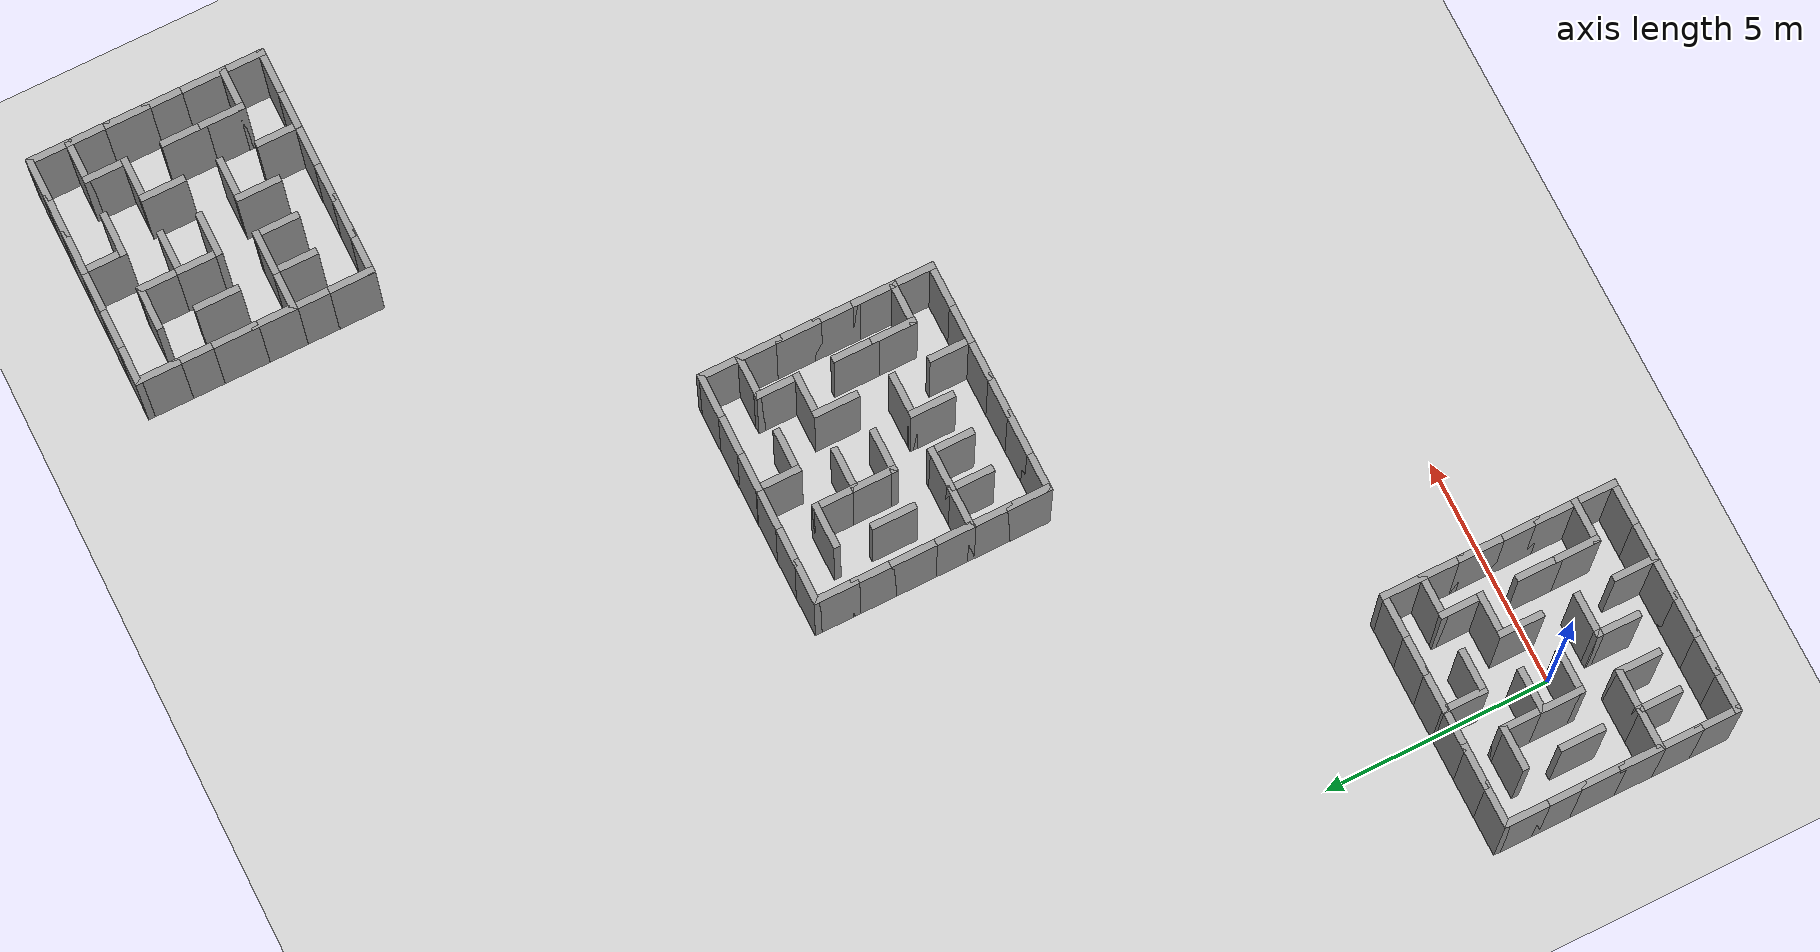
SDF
<sdf version="1.6">
 <world name="default">
  <include><uri>model://sun</uri></include>
  <include><uri>model://ground_plane</uri></include>
  <include><uri>model://maze</uri></include>
  <include><uri>model://maze</uri><pose>10 10 0 0 0 0</pose></include>
  <include><uri>model://maze</uri><pose>20 20 0 0 0 0</pose></include>
 </world>
</sdf>

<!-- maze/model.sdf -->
<sdf version='1.6'>
  <model name='maze'>
    <link name='Wall_102'>
      <pose>-2.55 -1.275 0 0 -0 1.5708</pose>
      <self_collide>0</self_collide>
      <enable_wind>0</enable_wind>
      <kinematic>0</kinematic>
      <visual name='Wall_102_Visual'>
        <pose>0 0 1.25 0 -0 0</pose>
        <geometry>
          <box>
            <size>1 0.15 2.5</size>
          </box>
        </geometry>
        <material>
          <script>
            <uri>file://media/materials/scripts/gazebo.material</uri>
            <name>Gazebo/Grey</name>
          </script>
          <ambient>1 1 1 1</ambient>
          <shader type='pixel'/>
        </material>
        <meta>
          <layer>0</layer>
        </meta>
        <transparency>0</transparency>
        <cast_shadows>1</cast_shadows>
      </visual>
      <collision name='Wall_102_Collision'>
        <laser_retro>0</laser_retro>
        <max_contacts>10</max_contacts>
        <pose>0 0 1.25 0 -0 0</pose>
        <geometry>
          <box>
            <size>1 0.15 2.5</size>
          </box>
        </geometry>
        <surface>
          <friction>
            <ode>
              <mu>1</mu>
              <mu2>1</mu2>
              <fdir1>0 0 0</fdir1>
              <slip1>0</slip1>
              <slip2>0</slip2>
            </ode>
            <torsional>
              <coefficient>1</coefficient>
              <patch_radius>0</patch_radius>
              <surface_radius>0</surface_radius>
              <use_patch_radius>1</use_patch_radius>
              <ode>
                <slip>0</slip>
              </ode>
            </torsional>
          </friction>
          <bounce>
            <restitution_coefficient>0</restitution_coefficient>
            <threshold>1e+06</threshold>
          </bounce>
          <contact>
            <collide_without_contact>0</collide_without_contact>
            <collide_without_contact_bitmask>1</collide_without_contact_bitmask>
            <collide_bitmask>1</collide_bitmask>
            <ode>
              <soft_cfm>0</soft_cfm>
              <soft_erp>0.2</soft_erp>
              <kp>1e+13</kp>
              <kd>1</kd>
              <max_vel>0.01</max_vel>
              <min_depth>0</min_depth>
            </ode>
            <bullet>
              <split_impulse>1</split_impulse>
              <split_impulse_penetration_threshold>-0.01</split_impulse_penetration_threshold>
              <soft_cfm>0</soft_cfm>
              <soft_erp>0.2</soft_erp>
              <kp>1e+13</kp>
              <kd>1</kd>
            </bullet>
          </contact>
        </surface>
      </collision>
    </link>
    <link name='Wall_103'>
      <pose>-2.125 -0.85 0 0 -0 0</pose>
      <self_collide>0</self_collide>
      <enable_wind>0</enable_wind>
      <kinematic>0</kinematic>
      <visual name='Wall_103_Visual'>
        <pose>0 0 1.25 0 -0 0</pose>
        <geometry>
          <box>
            <size>1 0.15 2.5</size>
          </box>
        </geometry>
        <material>
          <script>
            <uri>file://media/materials/scripts/gazebo.material</uri>
            <name>Gazebo/Grey</name>
          </script>
          <ambient>1 1 1 1</ambient>
          <shader type='pixel'/>
        </material>
        <meta>
          <layer>0</layer>
        </meta>
        <transparency>0</transparency>
        <cast_shadows>1</cast_shadows>
      </visual>
      <collision name='Wall_103_Collision'>
        <laser_retro>0</laser_retro>
        <max_contacts>10</max_contacts>
        <pose>0 0 1.25 0 -0 0</pose>
        <geometry>
          <box>
            <size>1 0.15 2.5</size>
          </box>
        </geometry>
        <surface>
          <friction>
            <ode>
              <mu>1</mu>
              <mu2>1</mu2>
              <fdir1>0 0 0</fdir1>
              <slip1>0</slip1>
              <slip2>0</slip2>
            </ode>
            <torsional>
              <coefficient>1</coefficient>
              <patch_radius>0</patch_radius>
              <surface_radius>0</surface_radius>
              <use_patch_radius>1</use_patch_radius>
              <ode>
                <slip>0</slip>
              </ode>
            </torsional>
          </friction>
          <bounce>
            <restitution_coefficient>0</restitution_coefficient>
            <threshold>1e+06</threshold>
          </bounce>
          <contact>
            <collide_without_contact>0</collide_without_contact>
            <collide_without_contact_bitmask>1</collide_without_contact_bitmask>
            <collide_bitmask>1</collide_bitmask>
            <ode>
              <soft_cfm>0</soft_cfm>
              <soft_erp>0.2</soft_erp>
              <kp>1e+13</kp>
              <kd>1</kd>
              <max_vel>0.01</max_vel>
              <min_depth>0</min_depth>
            </ode>
            <bullet>
              <split_impulse>1</split_impulse>
              <split_impulse_penetration_threshold>-0.01</split_impulse_penetration_threshold>
              <soft_cfm>0</soft_cfm>
              <soft_erp>0.2</soft_erp>
              <kp>1e+13</kp>
              <kd>1</kd>
            </bullet>
          </contact>
        </surface>
      </collision>
    </link>
    <link name='Wall_104'>
      <pose>-1.7 -1.275 0 0 0 -1.5708</pose>
      <self_collide>0</self_collide>
      <enable_wind>0</enable_wind>
      <kinematic>0</kinematic>
      <visual name='Wall_104_Visual'>
        <pose>0 0 1.25 0 -0 0</pose>
        <geometry>
          <box>
            <size>1 0.15 2.5</size>
          </box>
        </geometry>
        <material>
          <script>
            <uri>file://media/materials/scripts/gazebo.material</uri>
            <name>Gazebo/Grey</name>
          </script>
          <ambient>1 1 1 1</ambient>
          <shader type='pixel'/>
        </material>
        <meta>
          <layer>0</layer>
        </meta>
        <transparency>0</transparency>
        <cast_shadows>1</cast_shadows>
      </visual>
      <collision name='Wall_104_Collision'>
        <laser_retro>0</laser_retro>
        <max_contacts>10</max_contacts>
        <pose>0 0 1.25 0 -0 0</pose>
        <geometry>
          <box>
            <size>1 0.15 2.5</size>
          </box>
        </geometry>
        <surface>
          <friction>
            <ode>
              <mu>1</mu>
              <mu2>1</mu2>
              <fdir1>0 0 0</fdir1>
              <slip1>0</slip1>
              <slip2>0</slip2>
            </ode>
            <torsional>
              <coefficient>1</coefficient>
              <patch_radius>0</patch_radius>
              <surface_radius>0</surface_radius>
              <use_patch_radius>1</use_patch_radius>
              <ode>
                <slip>0</slip>
              </ode>
            </torsional>
          </friction>
          <bounce>
            <restitution_coefficient>0</restitution_coefficient>
            <threshold>1e+06</threshold>
          </bounce>
          <contact>
            <collide_without_contact>0</collide_without_contact>
            <collide_without_contact_bitmask>1</collide_without_contact_bitmask>
            <collide_bitmask>1</collide_bitmask>
            <ode>
              <soft_cfm>0</soft_cfm>
              <soft_erp>0.2</soft_erp>
              <kp>1e+13</kp>
              <kd>1</kd>
              <max_vel>0.01</max_vel>
              <min_depth>0</min_depth>
            </ode>
            <bullet>
              <split_impulse>1</split_impulse>
              <split_impulse_penetration_threshold>-0.01</split_impulse_penetration_threshold>
              <soft_cfm>0</soft_cfm>
              <soft_erp>0.2</soft_erp>
              <kp>1e+13</kp>
              <kd>1</kd>
            </bullet>
          </contact>
        </surface>
      </collision>
    </link>
    <link name='Wall_106'>
      <pose>-2.55 -2.125 0 0 0 -1.5708</pose>
      <self_collide>0</self_collide>
      <enable_wind>0</enable_wind>
      <kinematic>0</kinematic>
      <visual name='Wall_106_Visual'>
        <pose>0 0 1.25 0 -0 0</pose>
        <geometry>
          <box>
            <size>1 0.15 2.5</size>
          </box>
        </geometry>
        <material>
          <script>
            <uri>file://media/materials/scripts/gazebo.material</uri>
            <name>Gazebo/Grey</name>
          </script>
          <ambient>1 1 1 1</ambient>
          <shader type='pixel'/>
        </material>
        <meta>
          <layer>0</layer>
        </meta>
        <transparency>0</transparency>
        <cast_shadows>1</cast_shadows>
      </visual>
      <collision name='Wall_106_Collision'>
        <laser_retro>0</laser_retro>
        <max_contacts>10</max_contacts>
        <pose>0 0 1.25 0 -0 0</pose>
        <geometry>
          <box>
            <size>1 0.15 2.5</size>
          </box>
        </geometry>
        <surface>
          <friction>
            <ode>
              <mu>1</mu>
              <mu2>1</mu2>
              <fdir1>0 0 0</fdir1>
              <slip1>0</slip1>
              <slip2>0</slip2>
            </ode>
            <torsional>
              <coefficient>1</coefficient>
              <patch_radius>0</patch_radius>
              <surface_radius>0</surface_radius>
              <use_patch_radius>1</use_patch_radius>
              <ode>
                <slip>0</slip>
              </ode>
            </torsional>
          </friction>
          <bounce>
            <restitution_coefficient>0</restitution_coefficient>
            <threshold>1e+06</threshold>
          </bounce>
          <contact>
            <collide_without_contact>0</collide_without_contact>
            <collide_without_contact_bitmask>1</collide_without_contact_bitmask>
            <collide_bitmask>1</collide_bitmask>
            <ode>
              <soft_cfm>0</soft_cfm>
              <soft_erp>0.2</soft_erp>
              <kp>1e+13</kp>
              <kd>1</kd>
              <max_vel>0.01</max_vel>
              <min_depth>0</min_depth>
            </ode>
            <bullet>
              <split_impulse>1</split_impulse>
              <split_impulse_penetration_threshold>-0.01</split_impulse_penetration_threshold>
              <soft_cfm>0</soft_cfm>
              <soft_erp>0.2</soft_erp>
              <kp>1e+13</kp>
              <kd>1</kd>
            </bullet>
          </contact>
        </surface>
      </collision>
    </link>
    <link name='Wall_108'>
      <pose>-2.125 -2.55 0 0 -0 0</pose>
      <self_collide>0</self_collide>
      <enable_wind>0</enable_wind>
      <kinematic>0</kinematic>
      <visual name='Wall_108_Visual'>
        <pose>0 0 1.25 0 -0 0</pose>
        <geometry>
          <box>
            <size>1 0.15 2.5</size>
          </box>
        </geometry>
        <material>
          <script>
            <uri>file://media/materials/scripts/gazebo.material</uri>
            <name>Gazebo/Grey</name>
          </script>
          <ambient>1 1 1 1</ambient>
          <shader type='pixel'/>
        </material>
        <meta>
          <layer>0</layer>
        </meta>
        <transparency>0</transparency>
        <cast_shadows>1</cast_shadows>
      </visual>
      <collision name='Wall_108_Collision'>
        <laser_retro>0</laser_retro>
        <max_contacts>10</max_contacts>
        <pose>0 0 1.25 0 -0 0</pose>
        <geometry>
          <box>
            <size>1 0.15 2.5</size>
          </box>
        </geometry>
        <surface>
          <friction>
            <ode>
              <mu>1</mu>
              <mu2>1</mu2>
              <fdir1>0 0 0</fdir1>
              <slip1>0</slip1>
              <slip2>0</slip2>
            </ode>
            <torsional>
              <coefficient>1</coefficient>
              <patch_radius>0</patch_radius>
              <surface_radius>0</surface_radius>
              <use_patch_radius>1</use_patch_radius>
              <ode>
                <slip>0</slip>
              </ode>
            </torsional>
          </friction>
          <bounce>
            <restitution_coefficient>0</restitution_coefficient>
            <threshold>1e+06</threshold>
          </bounce>
          <contact>
            <collide_without_contact>0</collide_without_contact>
            <collide_without_contact_bitmask>1</collide_without_contact_bitmask>
            <collide_bitmask>1</collide_bitmask>
            <ode>
              <soft_cfm>0</soft_cfm>
              <soft_erp>0.2</soft_erp>
              <kp>1e+13</kp>
              <kd>1</kd>
              <max_vel>0.01</max_vel>
              <min_depth>0</min_depth>
            </ode>
            <bullet>
              <split_impulse>1</split_impulse>
              <split_impulse_penetration_threshold>-0.01</split_impulse_penetration_threshold>
              <soft_cfm>0</soft_cfm>
              <soft_erp>0.2</soft_erp>
              <kp>1e+13</kp>
              <kd>1</kd>
            </bullet>
          </contact>
        </surface>
      </collision>
    </link>
    <link name='Wall_111'>
      <pose>-0.85 -1.275 0 0 -0 1.5708</pose>
      <self_collide>0</self_collide>
      <enable_wind>0</enable_wind>
      <kinematic>0</kinematic>
      <visual name='Wall_111_Visual'>
        <pose>0 0 1.25 0 -0 0</pose>
        <geometry>
          <box>
            <size>1 0.15 2.5</size>
          </box>
        </geometry>
        <material>
          <script>
            <uri>file://media/materials/scripts/gazebo.material</uri>
            <name>Gazebo/Grey</name>
          </script>
          <ambient>1 1 1 1</ambient>
          <shader type='pixel'/>
        </material>
        <meta>
          <layer>0</layer>
        </meta>
        <transparency>0</transparency>
        <cast_shadows>1</cast_shadows>
      </visual>
      <collision name='Wall_111_Collision'>
        <laser_retro>0</laser_retro>
        <max_contacts>10</max_contacts>
        <pose>0 0 1.25 0 -0 0</pose>
        <geometry>
          <box>
            <size>1 0.15 2.5</size>
          </box>
        </geometry>
        <surface>
          <friction>
            <ode>
              <mu>1</mu>
              <mu2>1</mu2>
              <fdir1>0 0 0</fdir1>
              <slip1>0</slip1>
              <slip2>0</slip2>
            </ode>
            <torsional>
              <coefficient>1</coefficient>
              <patch_radius>0</patch_radius>
              <surface_radius>0</surface_radius>
              <use_patch_radius>1</use_patch_radius>
              <ode>
                <slip>0</slip>
              </ode>
            </torsional>
          </friction>
          <bounce>
            <restitution_coefficient>0</restitution_coefficient>
            <threshold>1e+06</threshold>
          </bounce>
          <contact>
            <collide_without_contact>0</collide_without_contact>
            <collide_without_contact_bitmask>1</collide_without_contact_bitmask>
            <collide_bitmask>1</collide_bitmask>
            <ode>
              <soft_cfm>0</soft_cfm>
              <soft_erp>0.2</soft_erp>
              <kp>1e+13</kp>
              <kd>1</kd>
              <max_vel>0.01</max_vel>
              <min_depth>0</min_depth>
            </ode>
            <bullet>
              <split_impulse>1</split_impulse>
              <split_impulse_penetration_threshold>-0.01</split_impulse_penetration_threshold>
              <soft_cfm>0</soft_cfm>
              <soft_erp>0.2</soft_erp>
              <kp>1e+13</kp>
              <kd>1</kd>
            </bullet>
          </contact>
        </surface>
      </collision>
    </link>
    <link name='Wall_112'>
      <pose>-1.275 -0.85 0 0 -0 3.14159</pose>
      <self_collide>0</self_collide>
      <enable_wind>0</enable_wind>
      <kinematic>0</kinematic>
      <visual name='Wall_112_Visual'>
        <pose>0 0 1.25 0 -0 0</pose>
        <geometry>
          <box>
            <size>1 0.15 2.5</size>
          </box>
        </geometry>
        <material>
          <script>
            <uri>file://media/materials/scripts/gazebo.material</uri>
            <name>Gazebo/Grey</name>
          </script>
          <ambient>1 1 1 1</ambient>
          <shader type='pixel'/>
        </material>
        <meta>
          <layer>0</layer>
        </meta>
        <transparency>0</transparency>
        <cast_shadows>1</cast_shadows>
      </visual>
      <collision name='Wall_112_Collision'>
        <laser_retro>0</laser_retro>
        <max_contacts>10</max_contacts>
        <pose>0 0 1.25 0 -0 0</pose>
        <geometry>
          <box>
            <size>1 0.15 2.5</size>
          </box>
        </geometry>
        <surface>
          <friction>
            <ode>
              <mu>1</mu>
              <mu2>1</mu2>
              <fdir1>0 0 0</fdir1>
              <slip1>0</slip1>
              <slip2>0</slip2>
            </ode>
            <torsional>
              <coefficient>1</coefficient>
              <patch_radius>0</patch_radius>
              <surface_radius>0</surface_radius>
              <use_patch_radius>1</use_patch_radius>
              <ode>
                <slip>0</slip>
              </ode>
            </torsional>
          </friction>
          <bounce>
            <restitution_coefficient>0</restitution_coefficient>
            <threshold>1e+06</threshold>
          </bounce>
          <contact>
            <collide_without_contact>0</collide_without_contact>
            <collide_without_contact_bitmask>1</collide_without_contact_bitmask>
            <collide_bitmask>1</collide_bitmask>
            <ode>
              <soft_cfm>0</soft_cfm>
              <soft_erp>0.2</soft_erp>
              <kp>1e+13</kp>
              <kd>1</kd>
              <max_vel>0.01</max_vel>
              <min_depth>0</min_depth>
            </ode>
            <bullet>
              <split_impulse>1</split_impulse>
              <split_impulse_penetration_threshold>-0.01</split_impulse_penetration_threshold>
              <soft_cfm>0</soft_cfm>
              <soft_erp>0.2</soft_erp>
              <kp>1e+13</kp>
              <kd>1</kd>
            </bullet>
          </contact>
        </surface>
      </collision>
    </link>
    <link name='Wall_118'>
      <pose>-0.425 0 0 0 -0 3.14159</pose>
      <self_collide>0</self_collide>
      <enable_wind>0</enable_wind>
      <kinematic>0</kinematic>
      <visual name='Wall_118_Visual'>
        <pose>0 0 1.25 0 -0 0</pose>
        <geometry>
          <box>
            <size>1 0.15 2.5</size>
          </box>
        </geometry>
        <material>
          <script>
            <uri>file://media/materials/scripts/gazebo.material</uri>
            <name>Gazebo/Grey</name>
          </script>
          <ambient>1 1 1 1</ambient>
          <shader type='pixel'/>
        </material>
        <meta>
          <layer>0</layer>
        </meta>
        <transparency>0</transparency>
        <cast_shadows>1</cast_shadows>
      </visual>
      <collision name='Wall_118_Collision'>
        <laser_retro>0</laser_retro>
        <max_contacts>10</max_contacts>
        <pose>0 0 1.25 0 -0 0</pose>
        <geometry>
          <box>
            <size>1 0.15 2.5</size>
          </box>
        </geometry>
        <surface>
          <friction>
            <ode>
              <mu>1</mu>
              <mu2>1</mu2>
              <fdir1>0 0 0</fdir1>
              <slip1>0</slip1>
              <slip2>0</slip2>
            </ode>
            <torsional>
              <coefficient>1</coefficient>
              <patch_radius>0</patch_radius>
              <surface_radius>0</surface_radius>
              <use_patch_radius>1</use_patch_radius>
              <ode>
                <slip>0</slip>
              </ode>
            </torsional>
          </friction>
          <bounce>
            <restitution_coefficient>0</restitution_coefficient>
            <threshold>1e+06</threshold>
          </bounce>
          <contact>
            <collide_without_contact>0</collide_without_contact>
            <collide_without_contact_bitmask>1</collide_without_contact_bitmask>
            <collide_bitmask>1</collide_bitmask>
            <ode>
              <soft_cfm>0</soft_cfm>
              <soft_erp>0.2</soft_erp>
              <kp>1e+13</kp>
              <kd>1</kd>
              <max_vel>0.01</max_vel>
              <min_depth>0</min_depth>
            </ode>
            <bullet>
              <split_impulse>1</split_impulse>
              <split_impulse_penetration_threshold>-0.01</split_impulse_penetration_threshold>
              <soft_cfm>0</soft_cfm>
              <soft_erp>0.2</soft_erp>
              <kp>1e+13</kp>
              <kd>1</kd>
            </bullet>
          </contact>
        </surface>
      </collision>
    </link>
    <link name='Wall_120'>
      <pose>-0.85 0.425 0 0 -0 1.5708</pose>
      <self_collide>0</self_collide>
      <enable_wind>0</enable_wind>
      <kinematic>0</kinematic>
      <visual name='Wall_120_Visual'>
        <pose>0 0 1.25 0 -0 0</pose>
        <geometry>
          <box>
            <size>1 0.15 2.5</size>
          </box>
        </geometry>
        <material>
          <script>
            <uri>file://media/materials/scripts/gazebo.material</uri>
            <name>Gazebo/Grey</name>
          </script>
          <ambient>1 1 1 1</ambient>
          <shader type='pixel'/>
        </material>
        <meta>
          <layer>0</layer>
        </meta>
        <transparency>0</transparency>
        <cast_shadows>1</cast_shadows>
      </visual>
      <collision name='Wall_120_Collision'>
        <laser_retro>0</laser_retro>
        <max_contacts>10</max_contacts>
        <pose>0 0 1.25 0 -0 0</pose>
        <geometry>
          <box>
            <size>1 0.15 2.5</size>
          </box>
        </geometry>
        <surface>
          <friction>
            <ode>
              <mu>1</mu>
              <mu2>1</mu2>
              <fdir1>0 0 0</fdir1>
              <slip1>0</slip1>
              <slip2>0</slip2>
            </ode>
            <torsional>
              <coefficient>1</coefficient>
              <patch_radius>0</patch_radius>
              <surface_radius>0</surface_radius>
              <use_patch_radius>1</use_patch_radius>
              <ode>
                <slip>0</slip>
              </ode>
            </torsional>
          </friction>
          <bounce>
            <restitution_coefficient>0</restitution_coefficient>
            <threshold>1e+06</threshold>
          </bounce>
          <contact>
            <collide_without_contact>0</collide_without_contact>
            <collide_without_contact_bitmask>1</collide_without_contact_bitmask>
            <collide_bitmask>1</collide_bitmask>
            <ode>
              <soft_cfm>0</soft_cfm>
              <soft_erp>0.2</soft_erp>
              <kp>1e+13</kp>
              <kd>1</kd>
              <max_vel>0.01</max_vel>
              <min_depth>0</min_depth>
            </ode>
            <bullet>
              <split_impulse>1</split_impulse>
              <split_impulse_penetration_threshold>-0.01</split_impulse_penetration_threshold>
              <soft_cfm>0</soft_cfm>
              <soft_erp>0.2</soft_erp>
              <kp>1e+13</kp>
              <kd>1</kd>
            </bullet>
          </contact>
        </surface>
      </collision>
    </link>
    <link name='Wall_121'>
      <pose>-0.425 0.85 0 0 -0 0</pose>
      <self_collide>0</self_collide>
      <enable_wind>0</enable_wind>
      <kinematic>0</kinematic>
      <visual name='Wall_121_Visual'>
        <pose>0 0 1.25 0 -0 0</pose>
        <geometry>
          <box>
            <size>1 0.15 2.5</size>
          </box>
        </geometry>
        <material>
          <script>
            <uri>file://media/materials/scripts/gazebo.material</uri>
            <name>Gazebo/Grey</name>
          </script>
          <ambient>1 1 1 1</ambient>
          <shader type='pixel'/>
        </material>
        <meta>
          <layer>0</layer>
        </meta>
        <transparency>0</transparency>
        <cast_shadows>1</cast_shadows>
      </visual>
      <collision name='Wall_121_Collision'>
        <laser_retro>0</laser_retro>
        <max_contacts>10</max_contacts>
        <pose>0 0 1.25 0 -0 0</pose>
        <geometry>
          <box>
            <size>1 0.15 2.5</size>
          </box>
        </geometry>
        <surface>
          <friction>
            <ode>
              <mu>1</mu>
              <mu2>1</mu2>
              <fdir1>0 0 0</fdir1>
              <slip1>0</slip1>
              <slip2>0</slip2>
            </ode>
            <torsional>
              <coefficient>1</coefficient>
              <patch_radius>0</patch_radius>
              <surface_radius>0</surface_radius>
              <use_patch_radius>1</use_patch_radius>
              <ode>
                <slip>0</slip>
              </ode>
            </torsional>
          </friction>
          <bounce>
            <restitution_coefficient>0</restitution_coefficient>
            <threshold>1e+06</threshold>
          </bounce>
          <contact>
            <collide_without_contact>0</collide_without_contact>
            <collide_without_contact_bitmask>1</collide_without_contact_bitmask>
            <collide_bitmask>1</collide_bitmask>
            <ode>
              <soft_cfm>0</soft_cfm>
              <soft_erp>0.2</soft_erp>
              <kp>1e+13</kp>
              <kd>1</kd>
              <max_vel>0.01</max_vel>
              <min_depth>0</min_depth>
            </ode>
            <bullet>
              <split_impulse>1</split_impulse>
              <split_impulse_penetration_threshold>-0.01</split_impulse_penetration_threshold>
              <soft_cfm>0</soft_cfm>
              <soft_erp>0.2</soft_erp>
              <kp>1e+13</kp>
              <kd>1</kd>
            </bullet>
          </contact>
        </surface>
      </collision>
    </link>
    <link name='Wall_124'>
      <pose>0.85 0.425 0 0 -0 1.5708</pose>
      <self_collide>0</self_collide>
      <enable_wind>0</enable_wind>
      <kinematic>0</kinematic>
      <visual name='Wall_124_Visual'>
        <pose>0 0 1.25 0 -0 0</pose>
        <geometry>
          <box>
            <size>1 0.15 2.5</size>
          </box>
        </geometry>
        <material>
          <script>
            <uri>file://media/materials/scripts/gazebo.material</uri>
            <name>Gazebo/Grey</name>
          </script>
          <ambient>1 1 1 1</ambient>
          <shader type='pixel'/>
        </material>
        <meta>
          <layer>0</layer>
        </meta>
        <transparency>0</transparency>
        <cast_shadows>1</cast_shadows>
      </visual>
      <collision name='Wall_124_Collision'>
        <laser_retro>0</laser_retro>
        <max_contacts>10</max_contacts>
        <pose>0 0 1.25 0 -0 0</pose>
        <geometry>
          <box>
            <size>1 0.15 2.5</size>
          </box>
        </geometry>
        <surface>
          <friction>
            <ode>
              <mu>1</mu>
              <mu2>1</mu2>
              <fdir1>0 0 0</fdir1>
              <slip1>0</slip1>
              <slip2>0</slip2>
            </ode>
            <torsional>
              <coefficient>1</coefficient>
              <patch_radius>0</patch_radius>
              <surface_radius>0</surface_radius>
              <use_patch_radius>1</use_patch_radius>
              <ode>
                <slip>0</slip>
              </ode>
            </torsional>
          </friction>
          <bounce>
            <restitution_coefficient>0</restitution_coefficient>
            <threshold>1e+06</threshold>
          </bounce>
          <contact>
            <collide_without_contact>0</collide_without_contact>
            <collide_without_contact_bitmask>1</collide_without_contact_bitmask>
            <collide_bitmask>1</collide_bitmask>
            <ode>
              <soft_cfm>0</soft_cfm>
              <soft_erp>0.2</soft_erp>
              <kp>1e+13</kp>
              <kd>1</kd>
              <max_vel>0.01</max_vel>
              <min_depth>0</min_depth>
            </ode>
            <bullet>
              <split_impulse>1</split_impulse>
              <split_impulse_penetration_threshold>-0.01</split_impulse_penetration_threshold>
              <soft_cfm>0</soft_cfm>
              <soft_erp>0.2</soft_erp>
              <kp>1e+13</kp>
              <kd>1</kd>
            </bullet>
          </contact>
        </surface>
      </collision>
    </link>
    <link name='Wall_127'>
      <pose>-1.275 -2.55 0 0 -0 0</pose>
      <self_collide>0</self_collide>
      <enable_wind>0</enable_wind>
      <kinematic>0</kinematic>
      <visual name='Wall_127_Visual'>
        <pose>0 0 1.25 0 -0 0</pose>
        <geometry>
          <box>
            <size>1 0.15 2.5</size>
          </box>
        </geometry>
        <material>
          <script>
            <uri>file://media/materials/scripts/gazebo.material</uri>
            <name>Gazebo/Grey</name>
          </script>
          <ambient>1 1 1 1</ambient>
          <shader type='pixel'/>
        </material>
        <meta>
          <layer>0</layer>
        </meta>
        <transparency>0</transparency>
        <cast_shadows>1</cast_shadows>
      </visual>
      <collision name='Wall_127_Collision'>
        <laser_retro>0</laser_retro>
        <max_contacts>10</max_contacts>
        <pose>0 0 1.25 0 -0 0</pose>
        <geometry>
          <box>
            <size>1 0.15 2.5</size>
          </box>
        </geometry>
        <surface>
          <friction>
            <ode>
              <mu>1</mu>
              <mu2>1</mu2>
              <fdir1>0 0 0</fdir1>
              <slip1>0</slip1>
              <slip2>0</slip2>
            </ode>
            <torsional>
              <coefficient>1</coefficient>
              <patch_radius>0</patch_radius>
              <surface_radius>0</surface_radius>
              <use_patch_radius>1</use_patch_radius>
              <ode>
                <slip>0</slip>
              </ode>
            </torsional>
          </friction>
          <bounce>
            <restitution_coefficient>0</restitution_coefficient>
            <threshold>1e+06</threshold>
          </bounce>
          <contact>
            <collide_without_contact>0</collide_without_contact>
            <collide_without_contact_bitmask>1</collide_without_contact_bitmask>
            <collide_bitmask>1</collide_bitmask>
            <ode>
              <soft_cfm>0</soft_cfm>
              <soft_erp>0.2</soft_erp>
              <kp>1e+13</kp>
              <kd>1</kd>
              <max_vel>0.01</max_vel>
              <min_depth>0</min_depth>
            </ode>
            <bullet>
              <split_impulse>1</split_impulse>
              <split_impulse_penetration_threshold>-0.01</split_impulse_penetration_threshold>
              <soft_cfm>0</soft_cfm>
              <soft_erp>0.2</soft_erp>
              <kp>1e+13</kp>
              <kd>1</kd>
            </bullet>
          </contact>
        </surface>
      </collision>
    </link>
    <link name='Wall_131'>
      <pose>-0.425 -2.55 0 0 -0 3.14159</pose>
      <self_collide>0</self_collide>
      <enable_wind>0</enable_wind>
      <kinematic>0</kinematic>
      <visual name='Wall_131_Visual'>
        <pose>0 0 1.25 0 -0 0</pose>
        <geometry>
          <box>
            <size>1 0.15 2.5</size>
          </box>
        </geometry>
        <material>
          <script>
            <uri>file://media/materials/scripts/gazebo.material</uri>
            <name>Gazebo/Grey</name>
          </script>
          <ambient>1 1 1 1</ambient>
          <shader type='pixel'/>
        </material>
        <meta>
          <layer>0</layer>
        </meta>
        <transparency>0</transparency>
        <cast_shadows>1</cast_shadows>
      </visual>
      <collision name='Wall_131_Collision'>
        <laser_retro>0</laser_retro>
        <max_contacts>10</max_contacts>
        <pose>0 0 1.25 0 -0 0</pose>
        <geometry>
          <box>
            <size>1 0.15 2.5</size>
          </box>
        </geometry>
        <surface>
          <friction>
            <ode>
              <mu>1</mu>
              <mu2>1</mu2>
              <fdir1>0 0 0</fdir1>
              <slip1>0</slip1>
              <slip2>0</slip2>
            </ode>
            <torsional>
              <coefficient>1</coefficient>
              <patch_radius>0</patch_radius>
              <surface_radius>0</surface_radius>
              <use_patch_radius>1</use_patch_radius>
              <ode>
                <slip>0</slip>
              </ode>
            </torsional>
          </friction>
          <bounce>
            <restitution_coefficient>0</restitution_coefficient>
            <threshold>1e+06</threshold>
          </bounce>
          <contact>
            <collide_without_contact>0</collide_without_contact>
            <collide_without_contact_bitmask>1</collide_without_contact_bitmask>
            <collide_bitmask>1</collide_bitmask>
            <ode>
              <soft_cfm>0</soft_cfm>
              <soft_erp>0.2</soft_erp>
              <kp>1e+13</kp>
              <kd>1</kd>
              <max_vel>0.01</max_vel>
              <min_depth>0</min_depth>
            </ode>
            <bullet>
              <split_impulse>1</split_impulse>
              <split_impulse_penetration_threshold>-0.01</split_impulse_penetration_threshold>
              <soft_cfm>0</soft_cfm>
              <soft_erp>0.2</soft_erp>
              <kp>1e+13</kp>
              <kd>1</kd>
            </bullet>
          </contact>
        </surface>
      </collision>
    </link>
    <link name='Wall_133'>
      <pose>0.425 -2.55 0 0 -0 0</pose>
      <self_collide>0</self_collide>
      <enable_wind>0</enable_wind>
      <kinematic>0</kinematic>
      <visual name='Wall_133_Visual'>
        <pose>0 0 1.25 0 -0 0</pose>
        <geometry>
          <box>
            <size>1 0.15 2.5</size>
          </box>
        </geometry>
        <material>
          <script>
            <uri>file://media/materials/scripts/gazebo.material</uri>
            <name>Gazebo/Grey</name>
          </script>
          <ambient>1 1 1 1</ambient>
          <shader type='pixel'/>
        </material>
        <meta>
          <layer>0</layer>
        </meta>
        <transparency>0</transparency>
        <cast_shadows>1</cast_shadows>
      </visual>
      <collision name='Wall_133_Collision'>
        <laser_retro>0</laser_retro>
        <max_contacts>10</max_contacts>
        <pose>0 0 1.25 0 -0 0</pose>
        <geometry>
          <box>
            <size>1 0.15 2.5</size>
          </box>
        </geometry>
        <surface>
          <friction>
            <ode>
              <mu>1</mu>
              <mu2>1</mu2>
              <fdir1>0 0 0</fdir1>
              <slip1>0</slip1>
              <slip2>0</slip2>
            </ode>
            <torsional>
              <coefficient>1</coefficient>
              <patch_radius>0</patch_radius>
              <surface_radius>0</surface_radius>
              <use_patch_radius>1</use_patch_radius>
              <ode>
                <slip>0</slip>
              </ode>
            </torsional>
          </friction>
          <bounce>
            <restitution_coefficient>0</restitution_coefficient>
            <threshold>1e+06</threshold>
          </bounce>
          <contact>
            <collide_without_contact>0</collide_without_contact>
            <collide_without_contact_bitmask>1</collide_without_contact_bitmask>
            <collide_bitmask>1</collide_bitmask>
            <ode>
              <soft_cfm>0</soft_cfm>
              <soft_erp>0.2</soft_erp>
              <kp>1e+13</kp>
              <kd>1</kd>
              <max_vel>0.01</max_vel>
              <min_depth>0</min_depth>
            </ode>
            <bullet>
              <split_impulse>1</split_impulse>
              <split_impulse_penetration_threshold>-0.01</split_impulse_penetration_threshold>
              <soft_cfm>0</soft_cfm>
              <soft_erp>0.2</soft_erp>
              <kp>1e+13</kp>
              <kd>1</kd>
            </bullet>
          </contact>
        </surface>
      </collision>
    </link>
    <link name='Wall_134'>
      <pose>0.85 -2.125 0 0 -0 1.5708</pose>
      <self_collide>0</self_collide>
      <enable_wind>0</enable_wind>
      <kinematic>0</kinematic>
      <visual name='Wall_134_Visual'>
        <pose>0 0 1.25 0 -0 0</pose>
        <geometry>
          <box>
            <size>1 0.15 2.5</size>
          </box>
        </geometry>
        <material>
          <script>
            <uri>file://media/materials/scripts/gazebo.material</uri>
            <name>Gazebo/Grey</name>
          </script>
          <ambient>1 1 1 1</ambient>
          <shader type='pixel'/>
        </material>
        <meta>
          <layer>0</layer>
        </meta>
        <transparency>0</transparency>
        <cast_shadows>1</cast_shadows>
      </visual>
      <collision name='Wall_134_Collision'>
        <laser_retro>0</laser_retro>
        <max_contacts>10</max_contacts>
        <pose>0 0 1.25 0 -0 0</pose>
        <geometry>
          <box>
            <size>1 0.15 2.5</size>
          </box>
        </geometry>
        <surface>
          <friction>
            <ode>
              <mu>1</mu>
              <mu2>1</mu2>
              <fdir1>0 0 0</fdir1>
              <slip1>0</slip1>
              <slip2>0</slip2>
            </ode>
            <torsional>
              <coefficient>1</coefficient>
              <patch_radius>0</patch_radius>
              <surface_radius>0</surface_radius>
              <use_patch_radius>1</use_patch_radius>
              <ode>
                <slip>0</slip>
              </ode>
            </torsional>
          </friction>
          <bounce>
            <restitution_coefficient>0</restitution_coefficient>
            <threshold>1e+06</threshold>
          </bounce>
          <contact>
            <collide_without_contact>0</collide_without_contact>
            <collide_without_contact_bitmask>1</collide_without_contact_bitmask>
            <collide_bitmask>1</collide_bitmask>
            <ode>
              <soft_cfm>0</soft_cfm>
              <soft_erp>0.2</soft_erp>
              <kp>1e+13</kp>
              <kd>1</kd>
              <max_vel>0.01</max_vel>
              <min_depth>0</min_depth>
            </ode>
            <bullet>
              <split_impulse>1</split_impulse>
              <split_impulse_penetration_threshold>-0.01</split_impulse_penetration_threshold>
              <soft_cfm>0</soft_cfm>
              <soft_erp>0.2</soft_erp>
              <kp>1e+13</kp>
              <kd>1</kd>
            </bullet>
          </contact>
        </surface>
      </collision>
    </link>
    <link name='Wall_136'>
      <pose>0 -1.275 0 0 -0 1.5708</pose>
      <self_collide>0</self_collide>
      <enable_wind>0</enable_wind>
      <kinematic>0</kinematic>
      <visual name='Wall_136_Visual'>
        <pose>0 0 1.25 0 -0 0</pose>
        <geometry>
          <box>
            <size>1 0.15 2.5</size>
          </box>
        </geometry>
        <material>
          <script>
            <uri>file://media/materials/scripts/gazebo.material</uri>
            <name>Gazebo/Grey</name>
          </script>
          <ambient>1 1 1 1</ambient>
          <shader type='pixel'/>
        </material>
        <meta>
          <layer>0</layer>
        </meta>
        <transparency>0</transparency>
        <cast_shadows>1</cast_shadows>
      </visual>
      <collision name='Wall_136_Collision'>
        <laser_retro>0</laser_retro>
        <max_contacts>10</max_contacts>
        <pose>0 0 1.25 0 -0 0</pose>
        <geometry>
          <box>
            <size>1 0.15 2.5</size>
          </box>
        </geometry>
        <surface>
          <friction>
            <ode>
              <mu>1</mu>
              <mu2>1</mu2>
              <fdir1>0 0 0</fdir1>
              <slip1>0</slip1>
              <slip2>0</slip2>
            </ode>
            <torsional>
              <coefficient>1</coefficient>
              <patch_radius>0</patch_radius>
              <surface_radius>0</surface_radius>
              <use_patch_radius>1</use_patch_radius>
              <ode>
                <slip>0</slip>
              </ode>
            </torsional>
          </friction>
          <bounce>
            <restitution_coefficient>0</restitution_coefficient>
            <threshold>1e+06</threshold>
          </bounce>
          <contact>
            <collide_without_contact>0</collide_without_contact>
            <collide_without_contact_bitmask>1</collide_without_contact_bitmask>
            <collide_bitmask>1</collide_bitmask>
            <ode>
              <soft_cfm>0</soft_cfm>
              <soft_erp>0.2</soft_erp>
              <kp>1e+13</kp>
              <kd>1</kd>
              <max_vel>0.01</max_vel>
              <min_depth>0</min_depth>
            </ode>
            <bullet>
              <split_impulse>1</split_impulse>
              <split_impulse_penetration_threshold>-0.01</split_impulse_penetration_threshold>
              <soft_cfm>0</soft_cfm>
              <soft_erp>0.2</soft_erp>
              <kp>1e+13</kp>
              <kd>1</kd>
            </bullet>
          </contact>
        </surface>
      </collision>
    </link>
    <link name='Wall_137'>
      <pose>0.425 -0.85 0 0 -0 0</pose>
      <self_collide>0</self_collide>
      <enable_wind>0</enable_wind>
      <kinematic>0</kinematic>
      <visual name='Wall_137_Visual'>
        <pose>0 0 1.25 0 -0 0</pose>
        <geometry>
          <box>
            <size>1 0.15 2.5</size>
          </box>
        </geometry>
        <material>
          <script>
            <uri>file://media/materials/scripts/gazebo.material</uri>
            <name>Gazebo/Grey</name>
          </script>
          <ambient>1 1 1 1</ambient>
          <shader type='pixel'/>
        </material>
        <meta>
          <layer>0</layer>
        </meta>
        <transparency>0</transparency>
        <cast_shadows>1</cast_shadows>
      </visual>
      <collision name='Wall_137_Collision'>
        <laser_retro>0</laser_retro>
        <max_contacts>10</max_contacts>
        <pose>0 0 1.25 0 -0 0</pose>
        <geometry>
          <box>
            <size>1 0.15 2.5</size>
          </box>
        </geometry>
        <surface>
          <friction>
            <ode>
              <mu>1</mu>
              <mu2>1</mu2>
              <fdir1>0 0 0</fdir1>
              <slip1>0</slip1>
              <slip2>0</slip2>
            </ode>
            <torsional>
              <coefficient>1</coefficient>
              <patch_radius>0</patch_radius>
              <surface_radius>0</surface_radius>
              <use_patch_radius>1</use_patch_radius>
              <ode>
                <slip>0</slip>
              </ode>
            </torsional>
          </friction>
          <bounce>
            <restitution_coefficient>0</restitution_coefficient>
            <threshold>1e+06</threshold>
          </bounce>
          <contact>
            <collide_without_contact>0</collide_without_contact>
            <collide_without_contact_bitmask>1</collide_without_contact_bitmask>
            <collide_bitmask>1</collide_bitmask>
            <ode>
              <soft_cfm>0</soft_cfm>
              <soft_erp>0.2</soft_erp>
              <kp>1e+13</kp>
              <kd>1</kd>
              <max_vel>0.01</max_vel>
              <min_depth>0</min_depth>
            </ode>
            <bullet>
              <split_impulse>1</split_impulse>
              <split_impulse_penetration_threshold>-0.01</split_impulse_penetration_threshold>
              <soft_cfm>0</soft_cfm>
              <soft_erp>0.2</soft_erp>
              <kp>1e+13</kp>
              <kd>1</kd>
            </bullet>
          </contact>
        </surface>
      </collision>
    </link>
    <link name='Wall_141'>
      <pose>1.275 -2.55 0 0 -0 3.14159</pose>
      <self_collide>0</self_collide>
      <enable_wind>0</enable_wind>
      <kinematic>0</kinematic>
      <visual name='Wall_141_Visual'>
        <pose>0 0 1.25 0 -0 0</pose>
        <geometry>
          <box>
            <size>1 0.15 2.5</size>
          </box>
        </geometry>
        <material>
          <script>
            <uri>file://media/materials/scripts/gazebo.material</uri>
            <name>Gazebo/Grey</name>
          </script>
          <ambient>1 1 1 1</ambient>
          <shader type='pixel'/>
        </material>
        <meta>
          <layer>0</layer>
        </meta>
        <transparency>0</transparency>
        <cast_shadows>1</cast_shadows>
      </visual>
      <collision name='Wall_141_Collision'>
        <laser_retro>0</laser_retro>
        <max_contacts>10</max_contacts>
        <pose>0 0 1.25 0 -0 0</pose>
        <geometry>
          <box>
            <size>1 0.15 2.5</size>
          </box>
        </geometry>
        <surface>
          <friction>
            <ode>
              <mu>1</mu>
              <mu2>1</mu2>
              <fdir1>0 0 0</fdir1>
              <slip1>0</slip1>
              <slip2>0</slip2>
            </ode>
            <torsional>
              <coefficient>1</coefficient>
              <patch_radius>0</patch_radius>
              <surface_radius>0</surface_radius>
              <use_patch_radius>1</use_patch_radius>
              <ode>
                <slip>0</slip>
              </ode>
            </torsional>
          </friction>
          <bounce>
            <restitution_coefficient>0</restitution_coefficient>
            <threshold>1e+06</threshold>
          </bounce>
          <contact>
            <collide_without_contact>0</collide_without_contact>
            <collide_without_contact_bitmask>1</collide_without_contact_bitmask>
            <collide_bitmask>1</collide_bitmask>
            <ode>
              <soft_cfm>0</soft_cfm>
              <soft_erp>0.2</soft_erp>
              <kp>1e+13</kp>
              <kd>1</kd>
              <max_vel>0.01</max_vel>
              <min_depth>0</min_depth>
            </ode>
            <bullet>
              <split_impulse>1</split_impulse>
              <split_impulse_penetration_threshold>-0.01</split_impulse_penetration_threshold>
              <soft_cfm>0</soft_cfm>
              <soft_erp>0.2</soft_erp>
              <kp>1e+13</kp>
              <kd>1</kd>
            </bullet>
          </contact>
        </surface>
      </collision>
    </link>
    <link name='Wall_145'>
      <pose>1.7 -1.275 0 0 0 -1.5708</pose>
      <self_collide>0</self_collide>
      <enable_wind>0</enable_wind>
      <kinematic>0</kinematic>
      <visual name='Wall_145_Visual'>
        <pose>0 0 1.25 0 -0 0</pose>
        <geometry>
          <box>
            <size>1 0.15 2.5</size>
          </box>
        </geometry>
        <material>
          <script>
            <uri>file://media/materials/scripts/gazebo.material</uri>
            <name>Gazebo/Grey</name>
          </script>
          <ambient>1 1 1 1</ambient>
          <shader type='pixel'/>
        </material>
        <meta>
          <layer>0</layer>
        </meta>
        <transparency>0</transparency>
        <cast_shadows>1</cast_shadows>
      </visual>
      <collision name='Wall_145_Collision'>
        <laser_retro>0</laser_retro>
        <max_contacts>10</max_contacts>
        <pose>0 0 1.25 0 -0 0</pose>
        <geometry>
          <box>
            <size>1 0.15 2.5</size>
          </box>
        </geometry>
        <surface>
          <friction>
            <ode>
              <mu>1</mu>
              <mu2>1</mu2>
              <fdir1>0 0 0</fdir1>
              <slip1>0</slip1>
              <slip2>0</slip2>
            </ode>
            <torsional>
              <coefficient>1</coefficient>
              <patch_radius>0</patch_radius>
              <surface_radius>0</surface_radius>
              <use_patch_radius>1</use_patch_radius>
              <ode>
                <slip>0</slip>
              </ode>
            </torsional>
          </friction>
          <bounce>
            <restitution_coefficient>0</restitution_coefficient>
            <threshold>1e+06</threshold>
          </bounce>
          <contact>
            <collide_without_contact>0</collide_without_contact>
            <collide_without_contact_bitmask>1</collide_without_contact_bitmask>
            <collide_bitmask>1</collide_bitmask>
            <ode>
              <soft_cfm>0</soft_cfm>
              <soft_erp>0.2</soft_erp>
              <kp>1e+13</kp>
              <kd>1</kd>
              <max_vel>0.01</max_vel>
              <min_depth>0</min_depth>
            </ode>
            <bullet>
              <split_impulse>1</split_impulse>
              <split_impulse_penetration_threshold>-0.01</split_impulse_penetration_threshold>
              <soft_cfm>0</soft_cfm>
              <soft_erp>0.2</soft_erp>
              <kp>1e+13</kp>
              <kd>1</kd>
            </bullet>
          </contact>
        </surface>
      </collision>
    </link>
    <link name='Wall_146'>
      <pose>2.125 -1.7 0 0 -0 0</pose>
      <self_collide>0</self_collide>
      <enable_wind>0</enable_wind>
      <kinematic>0</kinematic>
      <visual name='Wall_146_Visual'>
        <pose>0 0 1.25 0 -0 0</pose>
        <geometry>
          <box>
            <size>1 0.15 2.5</size>
          </box>
        </geometry>
        <material>
          <script>
            <uri>file://media/materials/scripts/gazebo.material</uri>
            <name>Gazebo/Grey</name>
          </script>
          <ambient>1 1 1 1</ambient>
          <shader type='pixel'/>
        </material>
        <meta>
          <layer>0</layer>
        </meta>
        <transparency>0</transparency>
        <cast_shadows>1</cast_shadows>
      </visual>
      <collision name='Wall_146_Collision'>
        <laser_retro>0</laser_retro>
        <max_contacts>10</max_contacts>
        <pose>0 0 1.25 0 -0 0</pose>
        <geometry>
          <box>
            <size>1 0.15 2.5</size>
          </box>
        </geometry>
        <surface>
          <friction>
            <ode>
              <mu>1</mu>
              <mu2>1</mu2>
              <fdir1>0 0 0</fdir1>
              <slip1>0</slip1>
              <slip2>0</slip2>
            </ode>
            <torsional>
              <coefficient>1</coefficient>
              <patch_radius>0</patch_radius>
              <surface_radius>0</surface_radius>
              <use_patch_radius>1</use_patch_radius>
              <ode>
                <slip>0</slip>
              </ode>
            </torsional>
          </friction>
          <bounce>
            <restitution_coefficient>0</restitution_coefficient>
            <threshold>1e+06</threshold>
          </bounce>
          <contact>
            <collide_without_contact>0</collide_without_contact>
            <collide_without_contact_bitmask>1</collide_without_contact_bitmask>
            <collide_bitmask>1</collide_bitmask>
            <ode>
              <soft_cfm>0</soft_cfm>
              <soft_erp>0.2</soft_erp>
              <kp>1e+13</kp>
              <kd>1</kd>
              <max_vel>0.01</max_vel>
              <min_depth>0</min_depth>
            </ode>
            <bullet>
              <split_impulse>1</split_impulse>
              <split_impulse_penetration_threshold>-0.01</split_impulse_penetration_threshold>
              <soft_cfm>0</soft_cfm>
              <soft_erp>0.2</soft_erp>
              <kp>1e+13</kp>
              <kd>1</kd>
            </bullet>
          </contact>
        </surface>
      </collision>
    </link>
    <link name='Wall_147'>
      <pose>2.55 -2.125 0 0 0 -1.5708</pose>
      <self_collide>0</self_collide>
      <enable_wind>0</enable_wind>
      <kinematic>0</kinematic>
      <visual name='Wall_147_Visual'>
        <pose>0 0 1.25 0 -0 0</pose>
        <geometry>
          <box>
            <size>1 0.15 2.5</size>
          </box>
        </geometry>
        <material>
          <script>
            <uri>file://media/materials/scripts/gazebo.material</uri>
            <name>Gazebo/Grey</name>
          </script>
          <ambient>1 1 1 1</ambient>
          <shader type='pixel'/>
        </material>
        <meta>
          <layer>0</layer>
        </meta>
        <transparency>0</transparency>
        <cast_shadows>1</cast_shadows>
      </visual>
      <collision name='Wall_147_Collision'>
        <laser_retro>0</laser_retro>
        <max_contacts>10</max_contacts>
        <pose>0 0 1.25 0 -0 0</pose>
        <geometry>
          <box>
            <size>1 0.15 2.5</size>
          </box>
        </geometry>
        <surface>
          <friction>
            <ode>
              <mu>1</mu>
              <mu2>1</mu2>
              <fdir1>0 0 0</fdir1>
              <slip1>0</slip1>
              <slip2>0</slip2>
            </ode>
            <torsional>
              <coefficient>1</coefficient>
              <patch_radius>0</patch_radius>
              <surface_radius>0</surface_radius>
              <use_patch_radius>1</use_patch_radius>
              <ode>
                <slip>0</slip>
              </ode>
            </torsional>
          </friction>
          <bounce>
            <restitution_coefficient>0</restitution_coefficient>
            <threshold>1e+06</threshold>
          </bounce>
          <contact>
            <collide_without_contact>0</collide_without_contact>
            <collide_without_contact_bitmask>1</collide_without_contact_bitmask>
            <collide_bitmask>1</collide_bitmask>
            <ode>
              <soft_cfm>0</soft_cfm>
              <soft_erp>0.2</soft_erp>
              <kp>1e+13</kp>
              <kd>1</kd>
              <max_vel>0.01</max_vel>
              <min_depth>0</min_depth>
            </ode>
            <bullet>
              <split_impulse>1</split_impulse>
              <split_impulse_penetration_threshold>-0.01</split_impulse_penetration_threshold>
              <soft_cfm>0</soft_cfm>
              <soft_erp>0.2</soft_erp>
              <kp>1e+13</kp>
              <kd>1</kd>
            </bullet>
          </contact>
        </surface>
      </collision>
    </link>
    <link name='Wall_148'>
      <pose>2.125 -2.55 0 0 -0 3.14159</pose>
      <self_collide>0</self_collide>
      <enable_wind>0</enable_wind>
      <kinematic>0</kinematic>
      <visual name='Wall_148_Visual'>
        <pose>0 0 1.25 0 -0 0</pose>
        <geometry>
          <box>
            <size>1 0.15 2.5</size>
          </box>
        </geometry>
        <material>
          <script>
            <uri>file://media/materials/scripts/gazebo.material</uri>
            <name>Gazebo/Grey</name>
          </script>
          <ambient>1 1 1 1</ambient>
          <shader type='pixel'/>
        </material>
        <meta>
          <layer>0</layer>
        </meta>
        <transparency>0</transparency>
        <cast_shadows>1</cast_shadows>
      </visual>
      <collision name='Wall_148_Collision'>
        <laser_retro>0</laser_retro>
        <max_contacts>10</max_contacts>
        <pose>0 0 1.25 0 -0 0</pose>
        <geometry>
          <box>
            <size>1 0.15 2.5</size>
          </box>
        </geometry>
        <surface>
          <friction>
            <ode>
              <mu>1</mu>
              <mu2>1</mu2>
              <fdir1>0 0 0</fdir1>
              <slip1>0</slip1>
              <slip2>0</slip2>
            </ode>
            <torsional>
              <coefficient>1</coefficient>
              <patch_radius>0</patch_radius>
              <surface_radius>0</surface_radius>
              <use_patch_radius>1</use_patch_radius>
              <ode>
                <slip>0</slip>
              </ode>
            </torsional>
          </friction>
          <bounce>
            <restitution_coefficient>0</restitution_coefficient>
            <threshold>1e+06</threshold>
          </bounce>
          <contact>
            <collide_without_contact>0</collide_without_contact>
            <collide_without_contact_bitmask>1</collide_without_contact_bitmask>
            <collide_bitmask>1</collide_bitmask>
            <ode>
              <soft_cfm>0</soft_cfm>
              <soft_erp>0.2</soft_erp>
              <kp>1e+13</kp>
              <kd>1</kd>
              <max_vel>0.01</max_vel>
              <min_depth>0</min_depth>
            </ode>
            <bullet>
              <split_impulse>1</split_impulse>
              <split_impulse_penetration_threshold>-0.01</split_impulse_penetration_threshold>
              <soft_cfm>0</soft_cfm>
              <soft_erp>0.2</soft_erp>
              <kp>1e+13</kp>
              <kd>1</kd>
            </bullet>
          </contact>
        </surface>
      </collision>
    </link>
    <link name='Wall_150'>
      <pose>1.275 0.85 0 0 -0 0</pose>
      <self_collide>0</self_collide>
      <enable_wind>0</enable_wind>
      <kinematic>0</kinematic>
      <visual name='Wall_150_Visual'>
        <pose>0 0 1.25 0 -0 0</pose>
        <geometry>
          <box>
            <size>1 0.15 2.5</size>
          </box>
        </geometry>
        <material>
          <script>
            <uri>file://media/materials/scripts/gazebo.material</uri>
            <name>Gazebo/Grey</name>
          </script>
          <ambient>1 1 1 1</ambient>
          <shader type='pixel'/>
        </material>
        <meta>
          <layer>0</layer>
        </meta>
        <transparency>0</transparency>
        <cast_shadows>1</cast_shadows>
      </visual>
      <collision name='Wall_150_Collision'>
        <laser_retro>0</laser_retro>
        <max_contacts>10</max_contacts>
        <pose>0 0 1.25 0 -0 0</pose>
        <geometry>
          <box>
            <size>1 0.15 2.5</size>
          </box>
        </geometry>
        <surface>
          <friction>
            <ode>
              <mu>1</mu>
              <mu2>1</mu2>
              <fdir1>0 0 0</fdir1>
              <slip1>0</slip1>
              <slip2>0</slip2>
            </ode>
            <torsional>
              <coefficient>1</coefficient>
              <patch_radius>0</patch_radius>
              <surface_radius>0</surface_radius>
              <use_patch_radius>1</use_patch_radius>
              <ode>
                <slip>0</slip>
              </ode>
            </torsional>
          </friction>
          <bounce>
            <restitution_coefficient>0</restitution_coefficient>
            <threshold>1e+06</threshold>
          </bounce>
          <contact>
            <collide_without_contact>0</collide_without_contact>
            <collide_without_contact_bitmask>1</collide_without_contact_bitmask>
            <collide_bitmask>1</collide_bitmask>
            <ode>
              <soft_cfm>0</soft_cfm>
              <soft_erp>0.2</soft_erp>
              <kp>1e+13</kp>
              <kd>1</kd>
              <max_vel>0.01</max_vel>
              <min_depth>0</min_depth>
            </ode>
            <bullet>
              <split_impulse>1</split_impulse>
              <split_impulse_penetration_threshold>-0.01</split_impulse_penetration_threshold>
              <soft_cfm>0</soft_cfm>
              <soft_erp>0.2</soft_erp>
              <kp>1e+13</kp>
              <kd>1</kd>
            </bullet>
          </contact>
        </surface>
      </collision>
    </link>
    <link name='Wall_154'>
      <pose>1.7 -0.425 0 0 0 -1.5708</pose>
      <self_collide>0</self_collide>
      <enable_wind>0</enable_wind>
      <kinematic>0</kinematic>
      <visual name='Wall_154_Visual'>
        <pose>0 0 1.25 0 -0 0</pose>
        <geometry>
          <box>
            <size>1 0.15 2.5</size>
          </box>
        </geometry>
        <material>
          <script>
            <uri>file://media/materials/scripts/gazebo.material</uri>
            <name>Gazebo/Grey</name>
          </script>
          <ambient>1 1 1 1</ambient>
          <shader type='pixel'/>
        </material>
        <meta>
          <layer>0</layer>
        </meta>
        <transparency>0</transparency>
        <cast_shadows>1</cast_shadows>
      </visual>
      <collision name='Wall_154_Collision'>
        <laser_retro>0</laser_retro>
        <max_contacts>10</max_contacts>
        <pose>0 0 1.25 0 -0 0</pose>
        <geometry>
          <box>
            <size>1 0.15 2.5</size>
          </box>
        </geometry>
        <surface>
          <friction>
            <ode>
              <mu>1</mu>
              <mu2>1</mu2>
              <fdir1>0 0 0</fdir1>
              <slip1>0</slip1>
              <slip2>0</slip2>
            </ode>
            <torsional>
              <coefficient>1</coefficient>
              <patch_radius>0</patch_radius>
              <surface_radius>0</surface_radius>
              <use_patch_radius>1</use_patch_radius>
              <ode>
                <slip>0</slip>
              </ode>
            </torsional>
          </friction>
          <bounce>
            <restitution_coefficient>0</restitution_coefficient>
            <threshold>1e+06</threshold>
          </bounce>
          <contact>
            <collide_without_contact>0</collide_without_contact>
            <collide_without_contact_bitmask>1</collide_without_contact_bitmask>
            <collide_bitmask>1</collide_bitmask>
            <ode>
              <soft_cfm>0</soft_cfm>
              <soft_erp>0.2</soft_erp>
              <kp>1e+13</kp>
              <kd>1</kd>
              <max_vel>0.01</max_vel>
              <min_depth>0</min_depth>
            </ode>
            <bullet>
              <split_impulse>1</split_impulse>
              <split_impulse_penetration_threshold>-0.01</split_impulse_penetration_threshold>
              <soft_cfm>0</soft_cfm>
              <soft_erp>0.2</soft_erp>
              <kp>1e+13</kp>
              <kd>1</kd>
            </bullet>
          </contact>
        </surface>
      </collision>
    </link>
    <link name='Wall_156'>
      <pose>2.55 -1.275 0 0 -0 1.5708</pose>
      <self_collide>0</self_collide>
      <enable_wind>0</enable_wind>
      <kinematic>0</kinematic>
      <visual name='Wall_156_Visual'>
        <pose>0 0 1.25 0 -0 0</pose>
        <geometry>
          <box>
            <size>1 0.15 2.5</size>
          </box>
        </geometry>
        <material>
          <script>
            <uri>file://media/materials/scripts/gazebo.material</uri>
            <name>Gazebo/Grey</name>
          </script>
          <ambient>1 1 1 1</ambient>
          <shader type='pixel'/>
        </material>
        <meta>
          <layer>0</layer>
        </meta>
        <transparency>0</transparency>
        <cast_shadows>1</cast_shadows>
      </visual>
      <collision name='Wall_156_Collision'>
        <laser_retro>0</laser_retro>
        <max_contacts>10</max_contacts>
        <pose>0 0 1.25 0 -0 0</pose>
        <geometry>
          <box>
            <size>1 0.15 2.5</size>
          </box>
        </geometry>
        <surface>
          <friction>
            <ode>
              <mu>1</mu>
              <mu2>1</mu2>
              <fdir1>0 0 0</fdir1>
              <slip1>0</slip1>
              <slip2>0</slip2>
            </ode>
            <torsional>
              <coefficient>1</coefficient>
              <patch_radius>0</patch_radius>
              <surface_radius>0</surface_radius>
              <use_patch_radius>1</use_patch_radius>
              <ode>
                <slip>0</slip>
              </ode>
            </torsional>
          </friction>
          <bounce>
            <restitution_coefficient>0</restitution_coefficient>
            <threshold>1e+06</threshold>
          </bounce>
          <contact>
            <collide_without_contact>0</collide_without_contact>
            <collide_without_contact_bitmask>1</collide_without_contact_bitmask>
            <collide_bitmask>1</collide_bitmask>
            <ode>
              <soft_cfm>0</soft_cfm>
              <soft_erp>0.2</soft_erp>
              <kp>1e+13</kp>
              <kd>1</kd>
              <max_vel>0.01</max_vel>
              <min_depth>0</min_depth>
            </ode>
            <bullet>
              <split_impulse>1</split_impulse>
              <split_impulse_penetration_threshold>-0.01</split_impulse_penetration_threshold>
              <soft_cfm>0</soft_cfm>
              <soft_erp>0.2</soft_erp>
              <kp>1e+13</kp>
              <kd>1</kd>
            </bullet>
          </contact>
        </surface>
      </collision>
    </link>
    <link name='Wall_160'>
      <pose>2.55 -0.425 0 0 0 -1.5708</pose>
      <self_collide>0</self_collide>
      <enable_wind>0</enable_wind>
      <kinematic>0</kinematic>
      <visual name='Wall_160_Visual'>
        <pose>0 0 1.25 0 -0 0</pose>
        <geometry>
          <box>
            <size>1 0.15 2.5</size>
          </box>
        </geometry>
        <material>
          <script>
            <uri>file://media/materials/scripts/gazebo.material</uri>
            <name>Gazebo/Grey</name>
          </script>
          <ambient>1 1 1 1</ambient>
          <shader type='pixel'/>
        </material>
        <meta>
          <layer>0</layer>
        </meta>
        <transparency>0</transparency>
        <cast_shadows>1</cast_shadows>
      </visual>
      <collision name='Wall_160_Collision'>
        <laser_retro>0</laser_retro>
        <max_contacts>10</max_contacts>
        <pose>0 0 1.25 0 -0 0</pose>
        <geometry>
          <box>
            <size>1 0.15 2.5</size>
          </box>
        </geometry>
        <surface>
          <friction>
            <ode>
              <mu>1</mu>
              <mu2>1</mu2>
              <fdir1>0 0 0</fdir1>
              <slip1>0</slip1>
              <slip2>0</slip2>
            </ode>
            <torsional>
              <coefficient>1</coefficient>
              <patch_radius>0</patch_radius>
              <surface_radius>0</surface_radius>
              <use_patch_radius>1</use_patch_radius>
              <ode>
                <slip>0</slip>
              </ode>
            </torsional>
          </friction>
          <bounce>
            <restitution_coefficient>0</restitution_coefficient>
            <threshold>1e+06</threshold>
          </bounce>
          <contact>
            <collide_without_contact>0</collide_without_contact>
            <collide_without_contact_bitmask>1</collide_without_contact_bitmask>
            <collide_bitmask>1</collide_bitmask>
            <ode>
              <soft_cfm>0</soft_cfm>
              <soft_erp>0.2</soft_erp>
              <kp>1e+13</kp>
              <kd>1</kd>
              <max_vel>0.01</max_vel>
              <min_depth>0</min_depth>
            </ode>
            <bullet>
              <split_impulse>1</split_impulse>
              <split_impulse_penetration_threshold>-0.01</split_impulse_penetration_threshold>
              <soft_cfm>0</soft_cfm>
              <soft_erp>0.2</soft_erp>
              <kp>1e+13</kp>
              <kd>1</kd>
            </bullet>
          </contact>
        </surface>
      </collision>
    </link>
    <link name='Wall_162'>
      <pose>2.55 0.425 0 0 -0 1.5708</pose>
      <self_collide>0</self_collide>
      <enable_wind>0</enable_wind>
      <kinematic>0</kinematic>
      <visual name='Wall_162_Visual'>
        <pose>0 0 1.25 0 -0 0</pose>
        <geometry>
          <box>
            <size>1 0.15 2.5</size>
          </box>
        </geometry>
        <material>
          <script>
            <uri>file://media/materials/scripts/gazebo.material</uri>
            <name>Gazebo/Grey</name>
          </script>
          <ambient>1 1 1 1</ambient>
          <shader type='pixel'/>
        </material>
        <meta>
          <layer>0</layer>
        </meta>
        <transparency>0</transparency>
        <cast_shadows>1</cast_shadows>
      </visual>
      <collision name='Wall_162_Collision'>
        <laser_retro>0</laser_retro>
        <max_contacts>10</max_contacts>
        <pose>0 0 1.25 0 -0 0</pose>
        <geometry>
          <box>
            <size>1 0.15 2.5</size>
          </box>
        </geometry>
        <surface>
          <friction>
            <ode>
              <mu>1</mu>
              <mu2>1</mu2>
              <fdir1>0 0 0</fdir1>
              <slip1>0</slip1>
              <slip2>0</slip2>
            </ode>
            <torsional>
              <coefficient>1</coefficient>
              <patch_radius>0</patch_radius>
              <surface_radius>0</surface_radius>
              <use_patch_radius>1</use_patch_radius>
              <ode>
                <slip>0</slip>
              </ode>
            </torsional>
          </friction>
          <bounce>
            <restitution_coefficient>0</restitution_coefficient>
            <threshold>1e+06</threshold>
          </bounce>
          <contact>
            <collide_without_contact>0</collide_without_contact>
            <collide_without_contact_bitmask>1</collide_without_contact_bitmask>
            <collide_bitmask>1</collide_bitmask>
            <ode>
              <soft_cfm>0</soft_cfm>
              <soft_erp>0.2</soft_erp>
              <kp>1e+13</kp>
              <kd>1</kd>
              <max_vel>0.01</max_vel>
              <min_depth>0</min_depth>
            </ode>
            <bullet>
              <split_impulse>1</split_impulse>
              <split_impulse_penetration_threshold>-0.01</split_impulse_penetration_threshold>
              <soft_cfm>0</soft_cfm>
              <soft_erp>0.2</soft_erp>
              <kp>1e+13</kp>
              <kd>1</kd>
            </bullet>
          </contact>
        </surface>
      </collision>
    </link>
    <link name='Wall_166'>
      <pose>-1.7 0.425 0 0 0 -1.5708</pose>
      <self_collide>0</self_collide>
      <enable_wind>0</enable_wind>
      <kinematic>0</kinematic>
      <visual name='Wall_166_Visual'>
        <pose>0 0 1.25 0 -0 0</pose>
        <geometry>
          <box>
            <size>1 0.15 2.5</size>
          </box>
        </geometry>
        <material>
          <script>
            <uri>file://media/materials/scripts/gazebo.material</uri>
            <name>Gazebo/Grey</name>
          </script>
          <ambient>1 1 1 1</ambient>
          <shader type='pixel'/>
        </material>
        <meta>
          <layer>0</layer>
        </meta>
        <transparency>0</transparency>
        <cast_shadows>1</cast_shadows>
      </visual>
      <collision name='Wall_166_Collision'>
        <laser_retro>0</laser_retro>
        <max_contacts>10</max_contacts>
        <pose>0 0 1.25 0 -0 0</pose>
        <geometry>
          <box>
            <size>1 0.15 2.5</size>
          </box>
        </geometry>
        <surface>
          <friction>
            <ode>
              <mu>1</mu>
              <mu2>1</mu2>
              <fdir1>0 0 0</fdir1>
              <slip1>0</slip1>
              <slip2>0</slip2>
            </ode>
            <torsional>
              <coefficient>1</coefficient>
              <patch_radius>0</patch_radius>
              <surface_radius>0</surface_radius>
              <use_patch_radius>1</use_patch_radius>
              <ode>
                <slip>0</slip>
              </ode>
            </torsional>
          </friction>
          <bounce>
            <restitution_coefficient>0</restitution_coefficient>
            <threshold>1e+06</threshold>
          </bounce>
          <contact>
            <collide_without_contact>0</collide_without_contact>
            <collide_without_contact_bitmask>1</collide_without_contact_bitmask>
            <collide_bitmask>1</collide_bitmask>
            <ode>
              <soft_cfm>0</soft_cfm>
              <soft_erp>0.2</soft_erp>
              <kp>1e+13</kp>
              <kd>1</kd>
              <max_vel>0.01</max_vel>
              <min_depth>0</min_depth>
            </ode>
            <bullet>
              <split_impulse>1</split_impulse>
              <split_impulse_penetration_threshold>-0.01</split_impulse_penetration_threshold>
              <soft_cfm>0</soft_cfm>
              <soft_erp>0.2</soft_erp>
              <kp>1e+13</kp>
              <kd>1</kd>
            </bullet>
          </contact>
        </surface>
      </collision>
    </link>
    <link name='Wall_169'>
      <pose>-2.55 0.425 0 0 0 -1.5708</pose>
      <self_collide>0</self_collide>
      <enable_wind>0</enable_wind>
      <kinematic>0</kinematic>
      <visual name='Wall_169_Visual'>
        <pose>0 0 1.25 0 -0 0</pose>
        <geometry>
          <box>
            <size>1 0.15 2.5</size>
          </box>
        </geometry>
        <material>
          <script>
            <uri>file://media/materials/scripts/gazebo.material</uri>
            <name>Gazebo/Grey</name>
          </script>
          <ambient>1 1 1 1</ambient>
          <shader type='pixel'/>
        </material>
        <meta>
          <layer>0</layer>
        </meta>
        <transparency>0</transparency>
        <cast_shadows>1</cast_shadows>
      </visual>
      <collision name='Wall_169_Collision'>
        <laser_retro>0</laser_retro>
        <max_contacts>10</max_contacts>
        <pose>0 0 1.25 0 -0 0</pose>
        <geometry>
          <box>
            <size>1 0.15 2.5</size>
          </box>
        </geometry>
        <surface>
          <friction>
            <ode>
              <mu>1</mu>
              <mu2>1</mu2>
              <fdir1>0 0 0</fdir1>
              <slip1>0</slip1>
              <slip2>0</slip2>
            </ode>
            <torsional>
              <coefficient>1</coefficient>
              <patch_radius>0</patch_radius>
              <surface_radius>0</surface_radius>
              <use_patch_radius>1</use_patch_radius>
              <ode>
                <slip>0</slip>
              </ode>
            </torsional>
          </friction>
          <bounce>
            <restitution_coefficient>0</restitution_coefficient>
            <threshold>1e+06</threshold>
          </bounce>
          <contact>
            <collide_without_contact>0</collide_without_contact>
            <collide_without_contact_bitmask>1</collide_without_contact_bitmask>
            <collide_bitmask>1</collide_bitmask>
            <ode>
              <soft_cfm>0</soft_cfm>
              <soft_erp>0.2</soft_erp>
              <kp>1e+13</kp>
              <kd>1</kd>
              <max_vel>0.01</max_vel>
              <min_depth>0</min_depth>
            </ode>
            <bullet>
              <split_impulse>1</split_impulse>
              <split_impulse_penetration_threshold>-0.01</split_impulse_penetration_threshold>
              <soft_cfm>0</soft_cfm>
              <soft_erp>0.2</soft_erp>
              <kp>1e+13</kp>
              <kd>1</kd>
            </bullet>
          </contact>
        </surface>
      </collision>
    </link>
    <link name='Wall_172'>
      <pose>-2.55 -0.425 0 0 0 -1.5708</pose>
      <self_collide>0</self_collide>
      <enable_wind>0</enable_wind>
      <kinematic>0</kinematic>
      <visual name='Wall_172_Visual'>
        <pose>0 0 1.25 0 -0 0</pose>
        <geometry>
          <box>
            <size>1 0.15 2.5</size>
          </box>
        </geometry>
        <material>
          <script>
            <uri>file://media/materials/scripts/gazebo.material</uri>
            <name>Gazebo/Grey</name>
          </script>
          <ambient>1 1 1 1</ambient>
          <shader type='pixel'/>
        </material>
        <meta>
          <layer>0</layer>
        </meta>
        <transparency>0</transparency>
        <cast_shadows>1</cast_shadows>
      </visual>
      <collision name='Wall_172_Collision'>
        <laser_retro>0</laser_retro>
        <max_contacts>10</max_contacts>
        <pose>0 0 1.25 0 -0 0</pose>
        <geometry>
          <box>
            <size>1 0.15 2.5</size>
          </box>
        </geometry>
        <surface>
          <friction>
            <ode>
              <mu>1</mu>
              <mu2>1</mu2>
              <fdir1>0 0 0</fdir1>
              <slip1>0</slip1>
              <slip2>0</slip2>
            </ode>
            <torsional>
              <coefficient>1</coefficient>
              <patch_radius>0</patch_radius>
              <surface_radius>0</surface_radius>
              <use_patch_radius>1</use_patch_radius>
              <ode>
                <slip>0</slip>
              </ode>
            </torsional>
          </friction>
          <bounce>
            <restitution_coefficient>0</restitution_coefficient>
            <threshold>1e+06</threshold>
          </bounce>
          <contact>
            <collide_without_contact>0</collide_without_contact>
            <collide_without_contact_bitmask>1</collide_without_contact_bitmask>
            <collide_bitmask>1</collide_bitmask>
            <ode>
              <soft_cfm>0</soft_cfm>
              <soft_erp>0.2</soft_erp>
              <kp>1e+13</kp>
              <kd>1</kd>
              <max_vel>0.01</max_vel>
              <min_depth>0</min_depth>
            </ode>
            <bullet>
              <split_impulse>1</split_impulse>
              <split_impulse_penetration_threshold>-0.01</split_impulse_penetration_threshold>
              <soft_cfm>0</soft_cfm>
              <soft_erp>0.2</soft_erp>
              <kp>1e+13</kp>
              <kd>1</kd>
            </bullet>
          </contact>
        </surface>
      </collision>
    </link>
    <link name='Wall_174'>
      <pose>-2.55 1.275 0 0 -0 1.5708</pose>
      <self_collide>0</self_collide>
      <enable_wind>0</enable_wind>
      <kinematic>0</kinematic>
      <visual name='Wall_174_Visual'>
        <pose>0 0 1.25 0 -0 0</pose>
        <geometry>
          <box>
            <size>1 0.15 2.5</size>
          </box>
        </geometry>
        <material>
          <script>
            <uri>file://media/materials/scripts/gazebo.material</uri>
            <name>Gazebo/Grey</name>
          </script>
          <ambient>1 1 1 1</ambient>
          <shader type='pixel'/>
        </material>
        <meta>
          <layer>0</layer>
        </meta>
        <transparency>0</transparency>
        <cast_shadows>1</cast_shadows>
      </visual>
      <collision name='Wall_174_Collision'>
        <laser_retro>0</laser_retro>
        <max_contacts>10</max_contacts>
        <pose>0 0 1.25 0 -0 0</pose>
        <geometry>
          <box>
            <size>1 0.15 2.5</size>
          </box>
        </geometry>
        <surface>
          <friction>
            <ode>
              <mu>1</mu>
              <mu2>1</mu2>
              <fdir1>0 0 0</fdir1>
              <slip1>0</slip1>
              <slip2>0</slip2>
            </ode>
            <torsional>
              <coefficient>1</coefficient>
              <patch_radius>0</patch_radius>
              <surface_radius>0</surface_radius>
              <use_patch_radius>1</use_patch_radius>
              <ode>
                <slip>0</slip>
              </ode>
            </torsional>
          </friction>
          <bounce>
            <restitution_coefficient>0</restitution_coefficient>
            <threshold>1e+06</threshold>
          </bounce>
          <contact>
            <collide_without_contact>0</collide_without_contact>
            <collide_without_contact_bitmask>1</collide_without_contact_bitmask>
            <collide_bitmask>1</collide_bitmask>
            <ode>
              <soft_cfm>0</soft_cfm>
              <soft_erp>0.2</soft_erp>
              <kp>1e+13</kp>
              <kd>1</kd>
              <max_vel>0.01</max_vel>
              <min_depth>0</min_depth>
            </ode>
            <bullet>
              <split_impulse>1</split_impulse>
              <split_impulse_penetration_threshold>-0.01</split_impulse_penetration_threshold>
              <soft_cfm>0</soft_cfm>
              <soft_erp>0.2</soft_erp>
              <kp>1e+13</kp>
              <kd>1</kd>
            </bullet>
          </contact>
        </surface>
      </collision>
    </link>
    <link name='Wall_177'>
      <pose>-2.125 2.55 0 0 -0 3.14159</pose>
      <self_collide>0</self_collide>
      <enable_wind>0</enable_wind>
      <kinematic>0</kinematic>
      <visual name='Wall_177_Visual'>
        <pose>0 0 1.25 0 -0 0</pose>
        <geometry>
          <box>
            <size>1 0.15 2.5</size>
          </box>
        </geometry>
        <material>
          <script>
            <uri>file://media/materials/scripts/gazebo.material</uri>
            <name>Gazebo/Grey</name>
          </script>
          <ambient>1 1 1 1</ambient>
          <shader type='pixel'/>
        </material>
        <meta>
          <layer>0</layer>
        </meta>
        <transparency>0</transparency>
        <cast_shadows>1</cast_shadows>
      </visual>
      <collision name='Wall_177_Collision'>
        <laser_retro>0</laser_retro>
        <max_contacts>10</max_contacts>
        <pose>0 0 1.25 0 -0 0</pose>
        <geometry>
          <box>
            <size>1 0.15 2.5</size>
          </box>
        </geometry>
        <surface>
          <friction>
            <ode>
              <mu>1</mu>
              <mu2>1</mu2>
              <fdir1>0 0 0</fdir1>
              <slip1>0</slip1>
              <slip2>0</slip2>
            </ode>
            <torsional>
              <coefficient>1</coefficient>
              <patch_radius>0</patch_radius>
              <surface_radius>0</surface_radius>
              <use_patch_radius>1</use_patch_radius>
              <ode>
                <slip>0</slip>
              </ode>
            </torsional>
          </friction>
          <bounce>
            <restitution_coefficient>0</restitution_coefficient>
            <threshold>1e+06</threshold>
          </bounce>
          <contact>
            <collide_without_contact>0</collide_without_contact>
            <collide_without_contact_bitmask>1</collide_without_contact_bitmask>
            <collide_bitmask>1</collide_bitmask>
            <ode>
              <soft_cfm>0</soft_cfm>
              <soft_erp>0.2</soft_erp>
              <kp>1e+13</kp>
              <kd>1</kd>
              <max_vel>0.01</max_vel>
              <min_depth>0</min_depth>
            </ode>
            <bullet>
              <split_impulse>1</split_impulse>
              <split_impulse_penetration_threshold>-0.01</split_impulse_penetration_threshold>
              <soft_cfm>0</soft_cfm>
              <soft_erp>0.2</soft_erp>
              <kp>1e+13</kp>
              <kd>1</kd>
            </bullet>
          </contact>
        </surface>
      </collision>
    </link>
    <link name='Wall_178'>
      <pose>-2.55 2.125 0 0 0 -1.5708</pose>
      <self_collide>0</self_collide>
      <enable_wind>0</enable_wind>
      <kinematic>0</kinematic>
      <visual name='Wall_178_Visual'>
        <pose>0 0 1.25 0 -0 0</pose>
        <geometry>
          <box>
            <size>1 0.15 2.5</size>
          </box>
        </geometry>
        <material>
          <script>
            <uri>file://media/materials/scripts/gazebo.material</uri>
            <name>Gazebo/Grey</name>
          </script>
          <ambient>1 1 1 1</ambient>
          <shader type='pixel'/>
        </material>
        <meta>
          <layer>0</layer>
        </meta>
        <transparency>0</transparency>
        <cast_shadows>1</cast_shadows>
      </visual>
      <collision name='Wall_178_Collision'>
        <laser_retro>0</laser_retro>
        <max_contacts>10</max_contacts>
        <pose>0 0 1.25 0 -0 0</pose>
        <geometry>
          <box>
            <size>1 0.15 2.5</size>
          </box>
        </geometry>
        <surface>
          <friction>
            <ode>
              <mu>1</mu>
              <mu2>1</mu2>
              <fdir1>0 0 0</fdir1>
              <slip1>0</slip1>
              <slip2>0</slip2>
            </ode>
            <torsional>
              <coefficient>1</coefficient>
              <patch_radius>0</patch_radius>
              <surface_radius>0</surface_radius>
              <use_patch_radius>1</use_patch_radius>
              <ode>
                <slip>0</slip>
              </ode>
            </torsional>
          </friction>
          <bounce>
            <restitution_coefficient>0</restitution_coefficient>
            <threshold>1e+06</threshold>
          </bounce>
          <contact>
            <collide_without_contact>0</collide_without_contact>
            <collide_without_contact_bitmask>1</collide_without_contact_bitmask>
            <collide_bitmask>1</collide_bitmask>
            <ode>
              <soft_cfm>0</soft_cfm>
              <soft_erp>0.2</soft_erp>
              <kp>1e+13</kp>
              <kd>1</kd>
              <max_vel>0.01</max_vel>
              <min_depth>0</min_depth>
            </ode>
            <bullet>
              <split_impulse>1</split_impulse>
              <split_impulse_penetration_threshold>-0.01</split_impulse_penetration_threshold>
              <soft_cfm>0</soft_cfm>
              <soft_erp>0.2</soft_erp>
              <kp>1e+13</kp>
              <kd>1</kd>
            </bullet>
          </contact>
        </surface>
      </collision>
    </link>
    <link name='Wall_181'>
      <pose>-1.275 1.7 0 0 -0 0</pose>
      <self_collide>0</self_collide>
      <enable_wind>0</enable_wind>
      <kinematic>0</kinematic>
      <visual name='Wall_181_Visual'>
        <pose>0 0 1.25 0 -0 0</pose>
        <geometry>
          <box>
            <size>1 0.15 2.5</size>
          </box>
        </geometry>
        <material>
          <script>
            <uri>file://media/materials/scripts/gazebo.material</uri>
            <name>Gazebo/Grey</name>
          </script>
          <ambient>1 1 1 1</ambient>
          <shader type='pixel'/>
        </material>
        <meta>
          <layer>0</layer>
        </meta>
        <transparency>0</transparency>
        <cast_shadows>1</cast_shadows>
      </visual>
      <collision name='Wall_181_Collision'>
        <laser_retro>0</laser_retro>
        <max_contacts>10</max_contacts>
        <pose>0 0 1.25 0 -0 0</pose>
        <geometry>
          <box>
            <size>1 0.15 2.5</size>
          </box>
        </geometry>
        <surface>
          <friction>
            <ode>
              <mu>1</mu>
              <mu2>1</mu2>
              <fdir1>0 0 0</fdir1>
              <slip1>0</slip1>
              <slip2>0</slip2>
            </ode>
            <torsional>
              <coefficient>1</coefficient>
              <patch_radius>0</patch_radius>
              <surface_radius>0</surface_radius>
              <use_patch_radius>1</use_patch_radius>
              <ode>
                <slip>0</slip>
              </ode>
            </torsional>
          </friction>
          <bounce>
            <restitution_coefficient>0</restitution_coefficient>
            <threshold>1e+06</threshold>
          </bounce>
          <contact>
            <collide_without_contact>0</collide_without_contact>
            <collide_without_contact_bitmask>1</collide_without_contact_bitmask>
            <collide_bitmask>1</collide_bitmask>
            <ode>
              <soft_cfm>0</soft_cfm>
              <soft_erp>0.2</soft_erp>
              <kp>1e+13</kp>
              <kd>1</kd>
              <max_vel>0.01</max_vel>
              <min_depth>0</min_depth>
            </ode>
            <bullet>
              <split_impulse>1</split_impulse>
              <split_impulse_penetration_threshold>-0.01</split_impulse_penetration_threshold>
              <soft_cfm>0</soft_cfm>
              <soft_erp>0.2</soft_erp>
              <kp>1e+13</kp>
              <kd>1</kd>
            </bullet>
          </contact>
        </surface>
      </collision>
    </link>
    <link name='Wall_183'>
      <pose>-1.275 2.55 0 0 -0 3.14159</pose>
      <self_collide>0</self_collide>
      <enable_wind>0</enable_wind>
      <kinematic>0</kinematic>
      <visual name='Wall_183_Visual'>
        <pose>0 0 1.25 0 -0 0</pose>
        <geometry>
          <box>
            <size>1 0.15 2.5</size>
          </box>
        </geometry>
        <material>
          <script>
            <uri>file://media/materials/scripts/gazebo.material</uri>
            <name>Gazebo/Grey</name>
          </script>
          <ambient>1 1 1 1</ambient>
          <shader type='pixel'/>
        </material>
        <meta>
          <layer>0</layer>
        </meta>
        <transparency>0</transparency>
        <cast_shadows>1</cast_shadows>
      </visual>
      <collision name='Wall_183_Collision'>
        <laser_retro>0</laser_retro>
        <max_contacts>10</max_contacts>
        <pose>0 0 1.25 0 -0 0</pose>
        <geometry>
          <box>
            <size>1 0.15 2.5</size>
          </box>
        </geometry>
        <surface>
          <friction>
            <ode>
              <mu>1</mu>
              <mu2>1</mu2>
              <fdir1>0 0 0</fdir1>
              <slip1>0</slip1>
              <slip2>0</slip2>
            </ode>
            <torsional>
              <coefficient>1</coefficient>
              <patch_radius>0</patch_radius>
              <surface_radius>0</surface_radius>
              <use_patch_radius>1</use_patch_radius>
              <ode>
                <slip>0</slip>
              </ode>
            </torsional>
          </friction>
          <bounce>
            <restitution_coefficient>0</restitution_coefficient>
            <threshold>1e+06</threshold>
          </bounce>
          <contact>
            <collide_without_contact>0</collide_without_contact>
            <collide_without_contact_bitmask>1</collide_without_contact_bitmask>
            <collide_bitmask>1</collide_bitmask>
            <ode>
              <soft_cfm>0</soft_cfm>
              <soft_erp>0.2</soft_erp>
              <kp>1e+13</kp>
              <kd>1</kd>
              <max_vel>0.01</max_vel>
              <min_depth>0</min_depth>
            </ode>
            <bullet>
              <split_impulse>1</split_impulse>
              <split_impulse_penetration_threshold>-0.01</split_impulse_penetration_threshold>
              <soft_cfm>0</soft_cfm>
              <soft_erp>0.2</soft_erp>
              <kp>1e+13</kp>
              <kd>1</kd>
            </bullet>
          </contact>
        </surface>
      </collision>
    </link>
    <link name='Wall_185'>
      <pose>-0.425 2.55 0 0 -0 0</pose>
      <self_collide>0</self_collide>
      <enable_wind>0</enable_wind>
      <kinematic>0</kinematic>
      <visual name='Wall_185_Visual'>
        <pose>0 0 1.25 0 -0 0</pose>
        <geometry>
          <box>
            <size>1 0.15 2.5</size>
          </box>
        </geometry>
        <material>
          <script>
            <uri>file://media/materials/scripts/gazebo.material</uri>
            <name>Gazebo/Grey</name>
          </script>
          <ambient>1 1 1 1</ambient>
          <shader type='pixel'/>
        </material>
        <meta>
          <layer>0</layer>
        </meta>
        <transparency>0</transparency>
        <cast_shadows>1</cast_shadows>
      </visual>
      <collision name='Wall_185_Collision'>
        <laser_retro>0</laser_retro>
        <max_contacts>10</max_contacts>
        <pose>0 0 1.25 0 -0 0</pose>
        <geometry>
          <box>
            <size>1 0.15 2.5</size>
          </box>
        </geometry>
        <surface>
          <friction>
            <ode>
              <mu>1</mu>
              <mu2>1</mu2>
              <fdir1>0 0 0</fdir1>
              <slip1>0</slip1>
              <slip2>0</slip2>
            </ode>
            <torsional>
              <coefficient>1</coefficient>
              <patch_radius>0</patch_radius>
              <surface_radius>0</surface_radius>
              <use_patch_radius>1</use_patch_radius>
              <ode>
                <slip>0</slip>
              </ode>
            </torsional>
          </friction>
          <bounce>
            <restitution_coefficient>0</restitution_coefficient>
            <threshold>1e+06</threshold>
          </bounce>
          <contact>
            <collide_without_contact>0</collide_without_contact>
            <collide_without_contact_bitmask>1</collide_without_contact_bitmask>
            <collide_bitmask>1</collide_bitmask>
            <ode>
              <soft_cfm>0</soft_cfm>
              <soft_erp>0.2</soft_erp>
              <kp>1e+13</kp>
              <kd>1</kd>
              <max_vel>0.01</max_vel>
              <min_depth>0</min_depth>
            </ode>
            <bullet>
              <split_impulse>1</split_impulse>
              <split_impulse_penetration_threshold>-0.01</split_impulse_penetration_threshold>
              <soft_cfm>0</soft_cfm>
              <soft_erp>0.2</soft_erp>
              <kp>1e+13</kp>
              <kd>1</kd>
            </bullet>
          </contact>
        </surface>
      </collision>
    </link>
    <link name='Wall_186'>
      <pose>0 2.125 0 0 0 -1.5708</pose>
      <self_collide>0</self_collide>
      <enable_wind>0</enable_wind>
      <kinematic>0</kinematic>
      <visual name='Wall_186_Visual'>
        <pose>0 0 1.25 0 -0 0</pose>
        <geometry>
          <box>
            <size>1 0.15 2.5</size>
          </box>
        </geometry>
        <material>
          <script>
            <uri>file://media/materials/scripts/gazebo.material</uri>
            <name>Gazebo/Grey</name>
          </script>
          <ambient>1 1 1 1</ambient>
          <shader type='pixel'/>
        </material>
        <meta>
          <layer>0</layer>
        </meta>
        <transparency>0</transparency>
        <cast_shadows>1</cast_shadows>
      </visual>
      <collision name='Wall_186_Collision'>
        <laser_retro>0</laser_retro>
        <max_contacts>10</max_contacts>
        <pose>0 0 1.25 0 -0 0</pose>
        <geometry>
          <box>
            <size>1 0.15 2.5</size>
          </box>
        </geometry>
        <surface>
          <friction>
            <ode>
              <mu>1</mu>
              <mu2>1</mu2>
              <fdir1>0 0 0</fdir1>
              <slip1>0</slip1>
              <slip2>0</slip2>
            </ode>
            <torsional>
              <coefficient>1</coefficient>
              <patch_radius>0</patch_radius>
              <surface_radius>0</surface_radius>
              <use_patch_radius>1</use_patch_radius>
              <ode>
                <slip>0</slip>
              </ode>
            </torsional>
          </friction>
          <bounce>
            <restitution_coefficient>0</restitution_coefficient>
            <threshold>1e+06</threshold>
          </bounce>
          <contact>
            <collide_without_contact>0</collide_without_contact>
            <collide_without_contact_bitmask>1</collide_without_contact_bitmask>
            <collide_bitmask>1</collide_bitmask>
            <ode>
              <soft_cfm>0</soft_cfm>
              <soft_erp>0.2</soft_erp>
              <kp>1e+13</kp>
              <kd>1</kd>
              <max_vel>0.01</max_vel>
              <min_depth>0</min_depth>
            </ode>
            <bullet>
              <split_impulse>1</split_impulse>
              <split_impulse_penetration_threshold>-0.01</split_impulse_penetration_threshold>
              <soft_cfm>0</soft_cfm>
              <soft_erp>0.2</soft_erp>
              <kp>1e+13</kp>
              <kd>1</kd>
            </bullet>
          </contact>
        </surface>
      </collision>
    </link>
    <link name='Wall_187'>
      <pose>0.425 1.7 0 0 -0 0</pose>
      <self_collide>0</self_collide>
      <enable_wind>0</enable_wind>
      <kinematic>0</kinematic>
      <visual name='Wall_187_Visual'>
        <pose>0 0 1.25 0 -0 0</pose>
        <geometry>
          <box>
            <size>1 0.15 2.5</size>
          </box>
        </geometry>
        <material>
          <script>
            <uri>file://media/materials/scripts/gazebo.material</uri>
            <name>Gazebo/Grey</name>
          </script>
          <ambient>1 1 1 1</ambient>
          <shader type='pixel'/>
        </material>
        <meta>
          <layer>0</layer>
        </meta>
        <transparency>0</transparency>
        <cast_shadows>1</cast_shadows>
      </visual>
      <collision name='Wall_187_Collision'>
        <laser_retro>0</laser_retro>
        <max_contacts>10</max_contacts>
        <pose>0 0 1.25 0 -0 0</pose>
        <geometry>
          <box>
            <size>1 0.15 2.5</size>
          </box>
        </geometry>
        <surface>
          <friction>
            <ode>
              <mu>1</mu>
              <mu2>1</mu2>
              <fdir1>0 0 0</fdir1>
              <slip1>0</slip1>
              <slip2>0</slip2>
            </ode>
            <torsional>
              <coefficient>1</coefficient>
              <patch_radius>0</patch_radius>
              <surface_radius>0</surface_radius>
              <use_patch_radius>1</use_patch_radius>
              <ode>
                <slip>0</slip>
              </ode>
            </torsional>
          </friction>
          <bounce>
            <restitution_coefficient>0</restitution_coefficient>
            <threshold>1e+06</threshold>
          </bounce>
          <contact>
            <collide_without_contact>0</collide_without_contact>
            <collide_without_contact_bitmask>1</collide_without_contact_bitmask>
            <collide_bitmask>1</collide_bitmask>
            <ode>
              <soft_cfm>0</soft_cfm>
              <soft_erp>0.2</soft_erp>
              <kp>1e+13</kp>
              <kd>1</kd>
              <max_vel>0.01</max_vel>
              <min_depth>0</min_depth>
            </ode>
            <bullet>
              <split_impulse>1</split_impulse>
              <split_impulse_penetration_threshold>-0.01</split_impulse_penetration_threshold>
              <soft_cfm>0</soft_cfm>
              <soft_erp>0.2</soft_erp>
              <kp>1e+13</kp>
              <kd>1</kd>
            </bullet>
          </contact>
        </surface>
      </collision>
    </link>
    <link name='Wall_189'>
      <pose>1.275 2.55 0 0 -0 0</pose>
      <self_collide>0</self_collide>
      <enable_wind>0</enable_wind>
      <kinematic>0</kinematic>
      <visual name='Wall_189_Visual'>
        <pose>0 0 1.25 0 -0 0</pose>
        <geometry>
          <box>
            <size>1 0.15 2.5</size>
          </box>
        </geometry>
        <material>
          <script>
            <uri>file://media/materials/scripts/gazebo.material</uri>
            <name>Gazebo/Grey</name>
          </script>
          <ambient>1 1 1 1</ambient>
          <shader type='pixel'/>
        </material>
        <meta>
          <layer>0</layer>
        </meta>
        <transparency>0</transparency>
        <cast_shadows>1</cast_shadows>
      </visual>
      <collision name='Wall_189_Collision'>
        <laser_retro>0</laser_retro>
        <max_contacts>10</max_contacts>
        <pose>0 0 1.25 0 -0 0</pose>
        <geometry>
          <box>
            <size>1 0.15 2.5</size>
          </box>
        </geometry>
        <surface>
          <friction>
            <ode>
              <mu>1</mu>
              <mu2>1</mu2>
              <fdir1>0 0 0</fdir1>
              <slip1>0</slip1>
              <slip2>0</slip2>
            </ode>
            <torsional>
              <coefficient>1</coefficient>
              <patch_radius>0</patch_radius>
              <surface_radius>0</surface_radius>
              <use_patch_radius>1</use_patch_radius>
              <ode>
                <slip>0</slip>
              </ode>
            </torsional>
          </friction>
          <bounce>
            <restitution_coefficient>0</restitution_coefficient>
            <threshold>1e+06</threshold>
          </bounce>
          <contact>
            <collide_without_contact>0</collide_without_contact>
            <collide_without_contact_bitmask>1</collide_without_contact_bitmask>
            <collide_bitmask>1</collide_bitmask>
            <ode>
              <soft_cfm>0</soft_cfm>
              <soft_erp>0.2</soft_erp>
              <kp>1e+13</kp>
              <kd>1</kd>
              <max_vel>0.01</max_vel>
              <min_depth>0</min_depth>
            </ode>
            <bullet>
              <split_impulse>1</split_impulse>
              <split_impulse_penetration_threshold>-0.01</split_impulse_penetration_threshold>
              <soft_cfm>0</soft_cfm>
              <soft_erp>0.2</soft_erp>
              <kp>1e+13</kp>
              <kd>1</kd>
            </bullet>
          </contact>
        </surface>
      </collision>
    </link>
    <link name='Wall_191'>
      <pose>2.125 1.7 0 0 -0 0</pose>
      <self_collide>0</self_collide>
      <enable_wind>0</enable_wind>
      <kinematic>0</kinematic>
      <visual name='Wall_191_Visual'>
        <pose>0 0 1.25 0 -0 0</pose>
        <geometry>
          <box>
            <size>1 0.15 2.5</size>
          </box>
        </geometry>
        <material>
          <script>
            <uri>file://media/materials/scripts/gazebo.material</uri>
            <name>Gazebo/Grey</name>
          </script>
          <ambient>1 1 1 1</ambient>
          <shader type='pixel'/>
        </material>
        <meta>
          <layer>0</layer>
        </meta>
        <transparency>0</transparency>
        <cast_shadows>1</cast_shadows>
      </visual>
      <collision name='Wall_191_Collision'>
        <laser_retro>0</laser_retro>
        <max_contacts>10</max_contacts>
        <pose>0 0 1.25 0 -0 0</pose>
        <geometry>
          <box>
            <size>1 0.15 2.5</size>
          </box>
        </geometry>
        <surface>
          <friction>
            <ode>
              <mu>1</mu>
              <mu2>1</mu2>
              <fdir1>0 0 0</fdir1>
              <slip1>0</slip1>
              <slip2>0</slip2>
            </ode>
            <torsional>
              <coefficient>1</coefficient>
              <patch_radius>0</patch_radius>
              <surface_radius>0</surface_radius>
              <use_patch_radius>1</use_patch_radius>
              <ode>
                <slip>0</slip>
              </ode>
            </torsional>
          </friction>
          <bounce>
            <restitution_coefficient>0</restitution_coefficient>
            <threshold>1e+06</threshold>
          </bounce>
          <contact>
            <collide_without_contact>0</collide_without_contact>
            <collide_without_contact_bitmask>1</collide_without_contact_bitmask>
            <collide_bitmask>1</collide_bitmask>
            <ode>
              <soft_cfm>0</soft_cfm>
              <soft_erp>0.2</soft_erp>
              <kp>1e+13</kp>
              <kd>1</kd>
              <max_vel>0.01</max_vel>
              <min_depth>0</min_depth>
            </ode>
            <bullet>
              <split_impulse>1</split_impulse>
              <split_impulse_penetration_threshold>-0.01</split_impulse_penetration_threshold>
              <soft_cfm>0</soft_cfm>
              <soft_erp>0.2</soft_erp>
              <kp>1e+13</kp>
              <kd>1</kd>
            </bullet>
          </contact>
        </surface>
      </collision>
    </link>
    <link name='Wall_192'>
      <pose>2.55 2.125 0 0 -0 1.5708</pose>
      <self_collide>0</self_collide>
      <enable_wind>0</enable_wind>
      <kinematic>0</kinematic>
      <visual name='Wall_192_Visual'>
        <pose>0 0 1.25 0 -0 0</pose>
        <geometry>
          <box>
            <size>1 0.15 2.5</size>
          </box>
        </geometry>
        <material>
          <script>
            <uri>file://media/materials/scripts/gazebo.material</uri>
            <name>Gazebo/Grey</name>
          </script>
          <ambient>1 1 1 1</ambient>
          <shader type='pixel'/>
        </material>
        <meta>
          <layer>0</layer>
        </meta>
        <transparency>0</transparency>
        <cast_shadows>1</cast_shadows>
      </visual>
      <collision name='Wall_192_Collision'>
        <laser_retro>0</laser_retro>
        <max_contacts>10</max_contacts>
        <pose>0 0 1.25 0 -0 0</pose>
        <geometry>
          <box>
            <size>1 0.15 2.5</size>
          </box>
        </geometry>
        <surface>
          <friction>
            <ode>
              <mu>1</mu>
              <mu2>1</mu2>
              <fdir1>0 0 0</fdir1>
              <slip1>0</slip1>
              <slip2>0</slip2>
            </ode>
            <torsional>
              <coefficient>1</coefficient>
              <patch_radius>0</patch_radius>
              <surface_radius>0</surface_radius>
              <use_patch_radius>1</use_patch_radius>
              <ode>
                <slip>0</slip>
              </ode>
            </torsional>
          </friction>
          <bounce>
            <restitution_coefficient>0</restitution_coefficient>
            <threshold>1e+06</threshold>
          </bounce>
          <contact>
            <collide_without_contact>0</collide_without_contact>
            <collide_without_contact_bitmask>1</collide_without_contact_bitmask>
            <collide_bitmask>1</collide_bitmask>
            <ode>
              <soft_cfm>0</soft_cfm>
              <soft_erp>0.2</soft_erp>
              <kp>1e+13</kp>
              <kd>1</kd>
              <max_vel>0.01</max_vel>
              <min_depth>0</min_depth>
            </ode>
            <bullet>
              <split_impulse>1</split_impulse>
              <split_impulse_penetration_threshold>-0.01</split_impulse_penetration_threshold>
              <soft_cfm>0</soft_cfm>
              <soft_erp>0.2</soft_erp>
              <kp>1e+13</kp>
              <kd>1</kd>
            </bullet>
          </contact>
        </surface>
      </collision>
    </link>
    <link name='Wall_193'>
      <pose>2.125 2.55 0 0 -0 3.14159</pose>
      <self_collide>0</self_collide>
      <enable_wind>0</enable_wind>
      <kinematic>0</kinematic>
      <visual name='Wall_193_Visual'>
        <pose>0 0 1.25 0 -0 0</pose>
        <geometry>
          <box>
            <size>1 0.15 2.5</size>
          </box>
        </geometry>
        <material>
          <script>
            <uri>file://media/materials/scripts/gazebo.material</uri>
            <name>Gazebo/Grey</name>
          </script>
          <ambient>1 1 1 1</ambient>
          <shader type='pixel'/>
        </material>
        <meta>
          <layer>0</layer>
        </meta>
        <transparency>0</transparency>
        <cast_shadows>1</cast_shadows>
      </visual>
      <collision name='Wall_193_Collision'>
        <laser_retro>0</laser_retro>
        <max_contacts>10</max_contacts>
        <pose>0 0 1.25 0 -0 0</pose>
        <geometry>
          <box>
            <size>1 0.15 2.5</size>
          </box>
        </geometry>
        <surface>
          <friction>
            <ode>
              <mu>1</mu>
              <mu2>1</mu2>
              <fdir1>0 0 0</fdir1>
              <slip1>0</slip1>
              <slip2>0</slip2>
            </ode>
            <torsional>
              <coefficient>1</coefficient>
              <patch_radius>0</patch_radius>
              <surface_radius>0</surface_radius>
              <use_patch_radius>1</use_patch_radius>
              <ode>
                <slip>0</slip>
              </ode>
            </torsional>
          </friction>
          <bounce>
            <restitution_coefficient>0</restitution_coefficient>
            <threshold>1e+06</threshold>
          </bounce>
          <contact>
            <collide_without_contact>0</collide_without_contact>
            <collide_without_contact_bitmask>1</collide_without_contact_bitmask>
            <collide_bitmask>1</collide_bitmask>
            <ode>
              <soft_cfm>0</soft_cfm>
              <soft_erp>0.2</soft_erp>
              <kp>1e+13</kp>
              <kd>1</kd>
              <max_vel>0.01</max_vel>
              <min_depth>0</min_depth>
            </ode>
            <bullet>
              <split_impulse>1</split_impulse>
              <split_impulse_penetration_threshold>-0.01</split_impulse_penetration_threshold>
              <soft_cfm>0</soft_cfm>
              <soft_erp>0.2</soft_erp>
              <kp>1e+13</kp>
              <kd>1</kd>
            </bullet>
          </contact>
        </surface>
      </collision>
    </link>
    <link name='Wall_195'>
      <pose>2.55 1.275 0 0 0 -1.5708</pose>
      <self_collide>0</self_collide>
      <enable_wind>0</enable_wind>
      <kinematic>0</kinematic>
      <visual name='Wall_195_Visual'>
        <pose>0 0 1.25 0 -0 0</pose>
        <geometry>
          <box>
            <size>1 0.15 2.5</size>
          </box>
        </geometry>
        <material>
          <script>
            <uri>file://media/materials/scripts/gazebo.material</uri>
            <name>Gazebo/Grey</name>
          </script>
          <ambient>1 1 1 1</ambient>
          <shader type='pixel'/>
        </material>
        <meta>
          <layer>0</layer>
        </meta>
        <transparency>0</transparency>
        <cast_shadows>1</cast_shadows>
      </visual>
      <collision name='Wall_195_Collision'>
        <laser_retro>0</laser_retro>
        <max_contacts>10</max_contacts>
        <pose>0 0 1.25 0 -0 0</pose>
        <geometry>
          <box>
            <size>1 0.15 2.5</size>
          </box>
        </geometry>
        <surface>
          <friction>
            <ode>
              <mu>1</mu>
              <mu2>1</mu2>
              <fdir1>0 0 0</fdir1>
              <slip1>0</slip1>
              <slip2>0</slip2>
            </ode>
            <torsional>
              <coefficient>1</coefficient>
              <patch_radius>0</patch_radius>
              <surface_radius>0</surface_radius>
              <use_patch_radius>1</use_patch_radius>
              <ode>
                <slip>0</slip>
              </ode>
            </torsional>
          </friction>
          <bounce>
            <restitution_coefficient>0</restitution_coefficient>
            <threshold>1e+06</threshold>
          </bounce>
          <contact>
            <collide_without_contact>0</collide_without_contact>
            <collide_without_contact_bitmask>1</collide_without_contact_bitmask>
            <collide_bitmask>1</collide_bitmask>
            <ode>
              <soft_cfm>0</soft_cfm>
              <soft_erp>0.2</soft_erp>
              <kp>1e+13</kp>
              <kd>1</kd>
              <max_vel>0.01</max_vel>
              <min_depth>0</min_depth>
            </ode>
            <bullet>
              <split_impulse>1</split_impulse>
              <split_impulse_penetration_threshold>-0.01</split_impulse_penetration_threshold>
              <soft_cfm>0</soft_cfm>
              <soft_erp>0.2</soft_erp>
              <kp>1e+13</kp>
              <kd>1</kd>
            </bullet>
          </contact>
        </surface>
      </collision>
    </link>
    <link name='Wall_197'>
      <pose>1.7 1.275 0 0 0 -1.5708</pose>
      <self_collide>0</self_collide>
      <enable_wind>0</enable_wind>
      <kinematic>0</kinematic>
      <visual name='Wall_197_Visual'>
        <pose>0 0 1.25 0 -0 0</pose>
        <geometry>
          <box>
            <size>1 0.15 2.5</size>
          </box>
        </geometry>
        <material>
          <script>
            <uri>file://media/materials/scripts/gazebo.material</uri>
            <name>Gazebo/Grey</name>
          </script>
          <ambient>1 1 1 1</ambient>
          <shader type='pixel'/>
        </material>
        <meta>
          <layer>0</layer>
        </meta>
        <transparency>0</transparency>
        <cast_shadows>1</cast_shadows>
      </visual>
      <collision name='Wall_197_Collision'>
        <laser_retro>0</laser_retro>
        <max_contacts>10</max_contacts>
        <pose>0 0 1.25 0 -0 0</pose>
        <geometry>
          <box>
            <size>1 0.15 2.5</size>
          </box>
        </geometry>
        <surface>
          <friction>
            <ode>
              <mu>1</mu>
              <mu2>1</mu2>
              <fdir1>0 0 0</fdir1>
              <slip1>0</slip1>
              <slip2>0</slip2>
            </ode>
            <torsional>
              <coefficient>1</coefficient>
              <patch_radius>0</patch_radius>
              <surface_radius>0</surface_radius>
              <use_patch_radius>1</use_patch_radius>
              <ode>
                <slip>0</slip>
              </ode>
            </torsional>
          </friction>
          <bounce>
            <restitution_coefficient>0</restitution_coefficient>
            <threshold>1e+06</threshold>
          </bounce>
          <contact>
            <collide_without_contact>0</collide_without_contact>
            <collide_without_contact_bitmask>1</collide_without_contact_bitmask>
            <collide_bitmask>1</collide_bitmask>
            <ode>
              <soft_cfm>0</soft_cfm>
              <soft_erp>0.2</soft_erp>
              <kp>1e+13</kp>
              <kd>1</kd>
              <max_vel>0.01</max_vel>
              <min_depth>0</min_depth>
            </ode>
            <bullet>
              <split_impulse>1</split_impulse>
              <split_impulse_penetration_threshold>-0.01</split_impulse_penetration_threshold>
              <soft_cfm>0</soft_cfm>
              <soft_erp>0.2</soft_erp>
              <kp>1e+13</kp>
              <kd>1</kd>
            </bullet>
          </contact>
        </surface>
      </collision>
    </link>
    <link name='Wall_199'>
      <pose>0.425 2.55 0 0 -0 0</pose>
      <self_collide>0</self_collide>
      <enable_wind>0</enable_wind>
      <kinematic>0</kinematic>
      <visual name='Wall_199_Visual'>
        <pose>0 0 1.25 0 -0 0</pose>
        <geometry>
          <box>
            <size>1 0.15 2.5</size>
          </box>
        </geometry>
        <material>
          <script>
            <uri>file://media/materials/scripts/gazebo.material</uri>
            <name>Gazebo/Grey</name>
          </script>
          <ambient>1 1 1 1</ambient>
          <shader type='pixel'/>
        </material>
        <meta>
          <layer>0</layer>
        </meta>
        <transparency>0</transparency>
        <cast_shadows>1</cast_shadows>
      </visual>
      <collision name='Wall_199_Collision'>
        <laser_retro>0</laser_retro>
        <max_contacts>10</max_contacts>
        <pose>0 0 1.25 0 -0 0</pose>
        <geometry>
          <box>
            <size>1 0.15 2.5</size>
          </box>
        </geometry>
        <surface>
          <friction>
            <ode>
              <mu>1</mu>
              <mu2>1</mu2>
              <fdir1>0 0 0</fdir1>
              <slip1>0</slip1>
              <slip2>0</slip2>
            </ode>
            <torsional>
              <coefficient>1</coefficient>
              <patch_radius>0</patch_radius>
              <surface_radius>0</surface_radius>
              <use_patch_radius>1</use_patch_radius>
              <ode>
                <slip>0</slip>
              </ode>
            </torsional>
          </friction>
          <bounce>
            <restitution_coefficient>0</restitution_coefficient>
            <threshold>1e+06</threshold>
          </bounce>
          <contact>
            <collide_without_contact>0</collide_without_contact>
            <collide_without_contact_bitmask>1</collide_without_contact_bitmask>
            <collide_bitmask>1</collide_bitmask>
            <ode>
              <soft_cfm>0</soft_cfm>
              <soft_erp>0.2</soft_erp>
              <kp>1e+13</kp>
              <kd>1</kd>
              <max_vel>0.01</max_vel>
              <min_depth>0</min_depth>
            </ode>
            <bullet>
              <split_impulse>1</split_impulse>
              <split_impulse_penetration_threshold>-0.01</split_impulse_penetration_threshold>
              <soft_cfm>0</soft_cfm>
              <soft_erp>0.2</soft_erp>
              <kp>1e+13</kp>
              <kd>1</kd>
            </bullet>
          </contact>
        </surface>
      </collision>
    </link>
    <link name='Wall_203'>
      <pose>-0.85 1.275 0 0 0 -1.5708</pose>
      <self_collide>0</self_collide>
      <enable_wind>0</enable_wind>
      <kinematic>0</kinematic>
      <visual name='Wall_203_Visual'>
        <pose>0 0 1.25 0 -0 0</pose>
        <geometry>
          <box>
            <size>1 0.15 2.5</size>
          </box>
        </geometry>
        <material>
          <script>
            <uri>file://media/materials/scripts/gazebo.material</uri>
            <name>Gazebo/Grey</name>
          </script>
          <ambient>1 1 1 1</ambient>
          <shader type='pixel'/>
        </material>
        <meta>
          <layer>0</layer>
        </meta>
        <transparency>0</transparency>
        <cast_shadows>1</cast_shadows>
      </visual>
      <collision name='Wall_203_Collision'>
        <laser_retro>0</laser_retro>
        <max_contacts>10</max_contacts>
        <pose>0 0 1.25 0 -0 0</pose>
        <geometry>
          <box>
            <size>1 0.15 2.5</size>
          </box>
        </geometry>
        <surface>
          <friction>
            <ode>
              <mu>1</mu>
              <mu2>1</mu2>
              <fdir1>0 0 0</fdir1>
              <slip1>0</slip1>
              <slip2>0</slip2>
            </ode>
            <torsional>
              <coefficient>1</coefficient>
              <patch_radius>0</patch_radius>
              <surface_radius>0</surface_radius>
              <use_patch_radius>1</use_patch_radius>
              <ode>
                <slip>0</slip>
              </ode>
            </torsional>
          </friction>
          <bounce>
            <restitution_coefficient>0</restitution_coefficient>
            <threshold>1e+06</threshold>
          </bounce>
          <contact>
            <collide_without_contact>0</collide_without_contact>
            <collide_without_contact_bitmask>1</collide_without_contact_bitmask>
            <collide_bitmask>1</collide_bitmask>
            <ode>
              <soft_cfm>0</soft_cfm>
              <soft_erp>0.2</soft_erp>
              <kp>1e+13</kp>
              <kd>1</kd>
              <max_vel>0.01</max_vel>
              <min_depth>0</min_depth>
            </ode>
            <bullet>
              <split_impulse>1</split_impulse>
              <split_impulse_penetration_threshold>-0.01</split_impulse_penetration_threshold>
              <soft_cfm>0</soft_cfm>
              <soft_erp>0.2</soft_erp>
              <kp>1e+13</kp>
              <kd>1</kd>
            </bullet>
          </contact>
        </surface>
      </collision>
    </link>
    <static>1</static>
    <allow_auto_disable>1</allow_auto_disable>
  </model>
</sdf>
